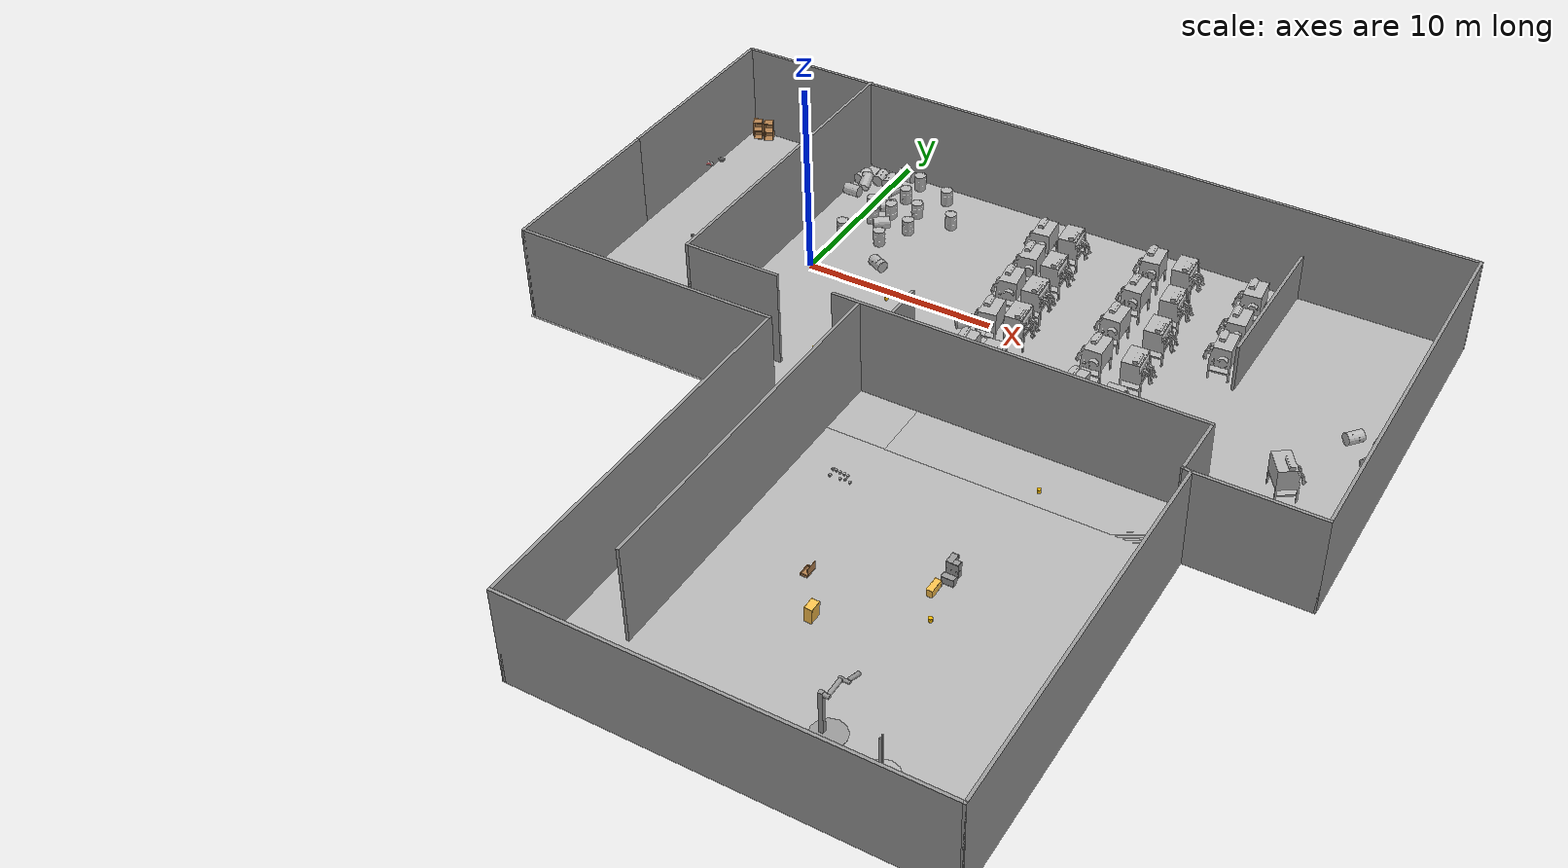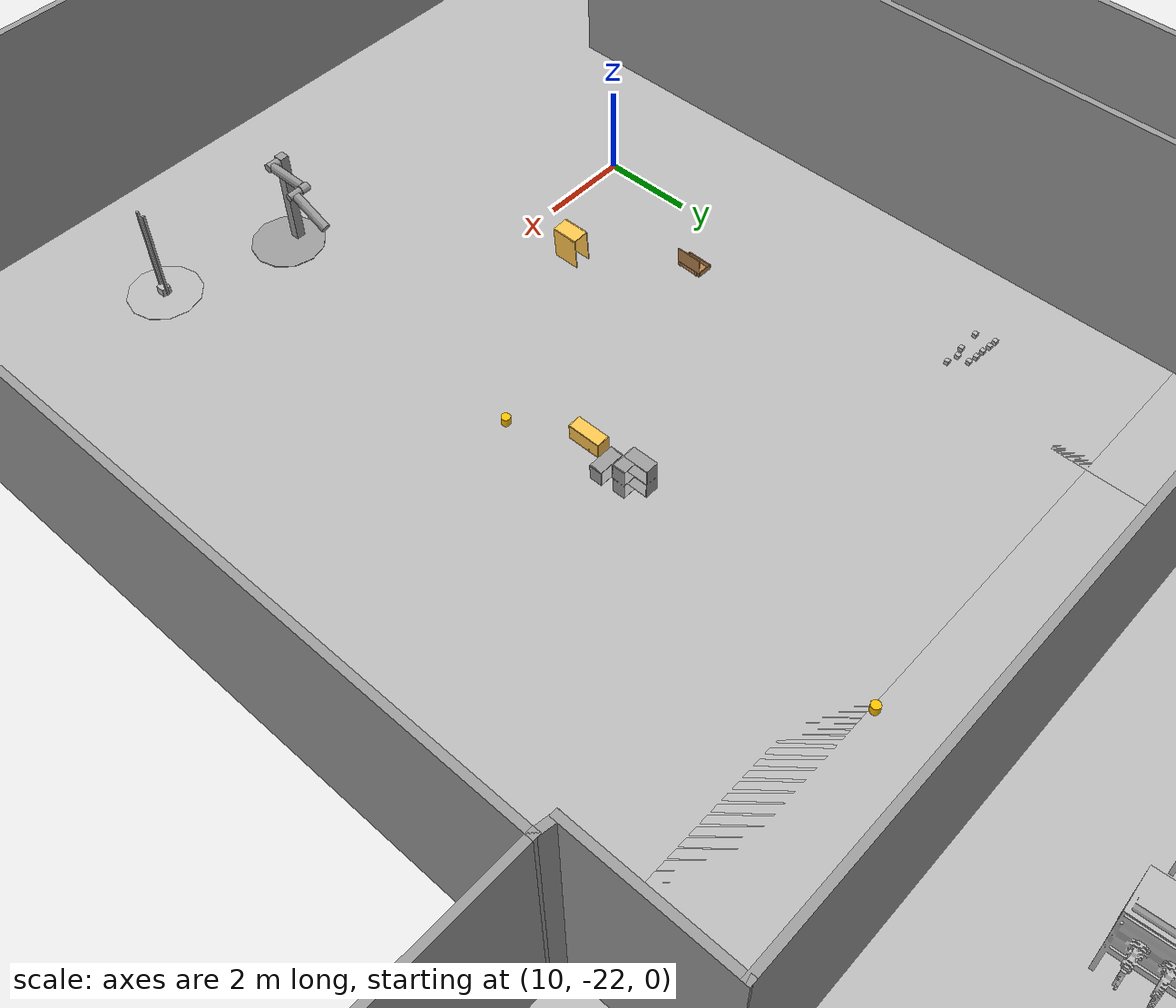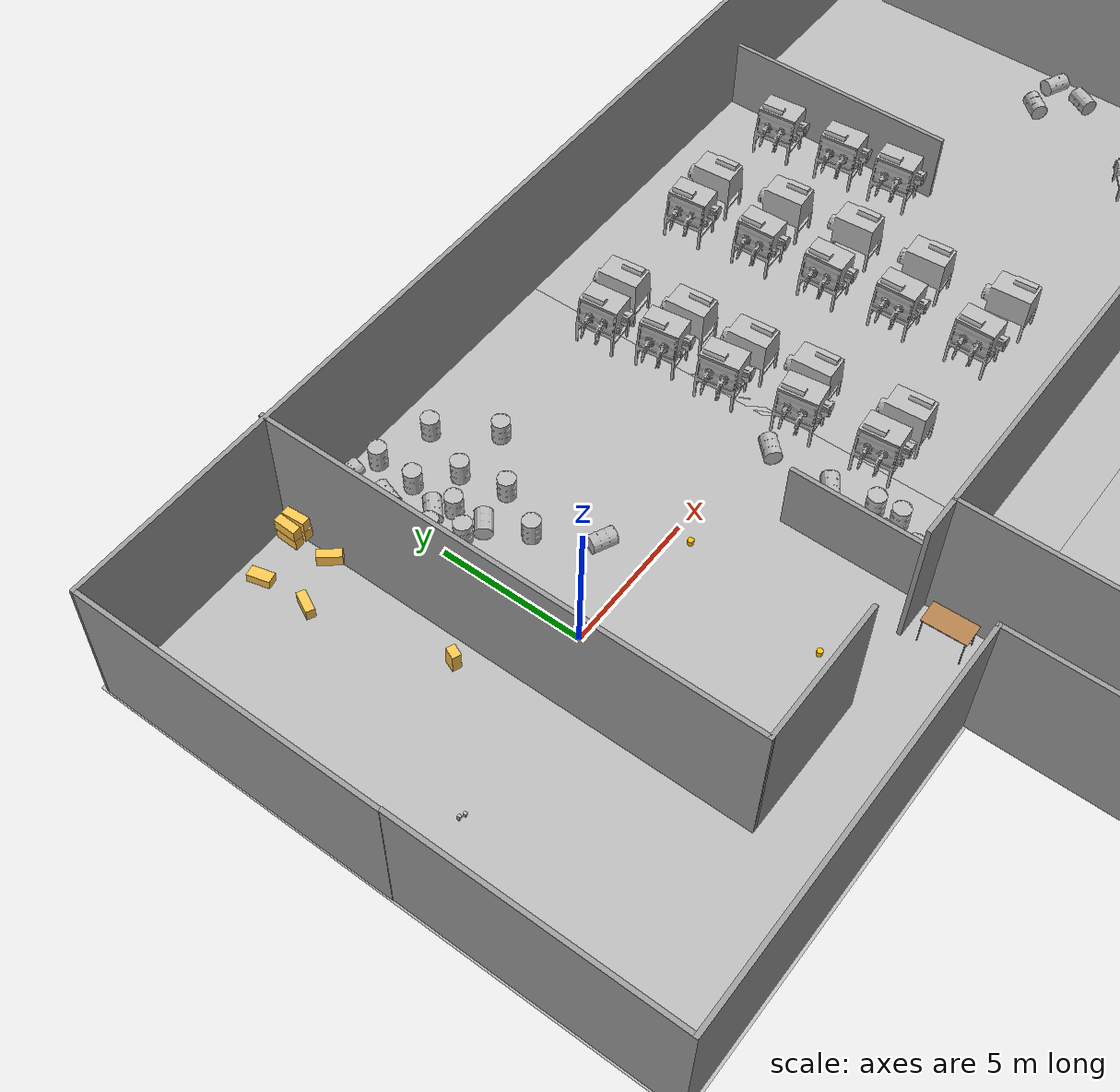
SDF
<sdf version="1.7">
 <world name="default">
  <light name="sun" type="directional">
   <pose>0 0 10 0 -0 0</pose>
   <diffuse>0.8 0.8 0.8 1</diffuse>
   <specular>0.2 0.2 0.2 1</specular>
   <attenuation>
    <range>1000</range>
    <constant>0.9</constant>
    <linear>0.01</linear>
    <quadratic>0.001</quadratic>
   </attenuation>
   <direction>-0.5 0.1 -0.9</direction>
   <spot><inner_angle>0</inner_angle><outer_angle>0</outer_angle><falloff>0</falloff></spot>
  </light>
  <model name="ground_plane">
   <static>1</static>
   <link name="link">
    <collision name="collision">
     <geometry><plane><normal>0 0 1</normal><size>100 100</size></plane></geometry>
     <surface><friction><ode><mu>100</mu><mu2>50</mu2></ode></friction></surface>
    </collision>
    <visual name="visual">
     <cast_shadows>0</cast_shadows>
     <geometry><plane><normal>0 0 1</normal><size>100 100</size></plane></geometry>
     <material>
      <script><uri>file://media/materials/scripts/gazebo.material</uri><name>Gazebo/Grey</name></script>
     </material>
    </visual>
   </link>
  </model>
  <gravity>0 0 -9.8</gravity>
  <magnetic_field>6e-06 2.3e-05 -4.2e-05</magnetic_field>
  <atmosphere type="adiabatic"/>
  <physics type="ode">
   <max_step_size>0.001</max_step_size>
   <real_time_factor>1</real_time_factor>
   <real_time_update_rate>1000</real_time_update_rate>
  </physics>
  <scene><ambient>0.4 0.4 0.4 1</ambient><background>0.7 0.7 0.7 1</background><shadows>1</shadows></scene>
  <audio><device>default</device></audio>
  <spherical_coordinates>
   <surface_model>EARTH_WGS84</surface_model>
   <latitude_deg>0</latitude_deg>
   <longitude_deg>0</longitude_deg>
   <elevation>0</elevation>
   <heading_deg>0</heading_deg>
  </spherical_coordinates>
  <model name="large_room_demo">
   <pose>10.4026 -9.94141 0 0 -0 0</pose>
   <link name="Wall_1">
    <collision name="Wall_1_Collision">
     <geometry><box><size>9.25 0.15 5</size></box></geometry>
     <pose>0 0 2.5 0 -0 0</pose>
    </collision>
    <visual name="Wall_1_Visual">
     <pose>0 0 2.5 0 -0 0</pose>
     <geometry><box><size>9.25 0.15 5</size></box></geometry>
     <material>
      <script><uri>file://media/materials/scripts/gazebo.material</uri><name>Gazebo/Grey</name></script>
      <ambient>1 1 1 1</ambient>
     </material>
     <meta><layer>0</layer></meta>
    </visual>
    <pose>-19.766 4.391 0 0 -0 -1.5708</pose>
   </link>
   <link name="Wall_11">
    <collision name="Wall_11_Collision">
     <geometry><box><size>17 0.15 5</size></box></geometry>
     <pose>0 0 2.5 0 -0 0</pose>
    </collision>
    <visual name="Wall_11_Visual">
     <pose>0 0 2.5 0 -0 0</pose>
     <geometry><box><size>17 0.15 5</size></box></geometry>
     <material>
      <script><uri>file://media/materials/scripts/gazebo.material</uri><name>Gazebo/Grey</name></script>
      <ambient>1 1 1 1</ambient>
     </material>
     <meta><layer>0</layer></meta>
    </visual>
    <pose>-12.466 11.084 0 0 -0 -1.5708</pose>
   </link>
   <link name="Wall_12">
    <collision name="Wall_12_Collision">
     <geometry><box><size>5 0.15 5</size></box></geometry>
     <pose>0 0 2.5 0 -0 0</pose>
    </collision>
    <visual name="Wall_12_Visual">
     <pose>0 0 2.5 0 -0 0</pose>
     <geometry><box><size>5 0.15 5</size></box></geometry>
     <material>
      <script><uri>file://media/materials/scripts/gazebo.material</uri><name>Gazebo/Grey</name></script>
      <ambient>1 1 1 1</ambient>
     </material>
     <meta><layer>0</layer></meta>
    </visual>
    <pose>-10.041 2.659 0 0 -0 0</pose>
   </link>
   <link name="Wall_15">
    <collision name="Wall_15_Collision">
     <geometry><box><size>1.5 0.15 5</size></box></geometry>
     <pose>0 0 2.5 0 -0 0</pose>
    </collision>
    <visual name="Wall_15_Visual">
     <pose>0 0 2.5 0 -0 0</pose>
     <geometry><box><size>1.5 0.15 5</size></box></geometry>
     <material>
      <script><uri>file://media/materials/scripts/gazebo.material</uri><name>Gazebo/Grey</name></script>
      <ambient>1 1 1 1</ambient>
     </material>
     <meta><layer>0</layer></meta>
    </visual>
    <pose>-3.97 2.751 0 0 -0 0</pose>
   </link>
   <link name="Wall_16">
    <collision name="Wall_16_Collision">
     <geometry><box><size>18.2497 0.15 5</size></box></geometry>
     <pose>0 0 2.5 0 -0 0</pose>
    </collision>
    <visual name="Wall_16_Visual">
     <pose>0 0 2.5 0 -0 0</pose>
     <geometry><box><size>18.2497 0.15 5</size></box></geometry>
     <material>
      <script><uri>file://media/materials/scripts/gazebo.material</uri><name>Gazebo/Grey</name></script>
      <ambient>1 1 1 1</ambient>
     </material>
     <meta><layer>0</layer></meta>
    </visual>
    <pose>-3.295 -6.299 0 0 -0 -1.5708</pose>
   </link>
   <link name="Wall_18">
    <collision name="Wall_18_Collision">
     <geometry><box><size>17 0.15 5</size></box></geometry>
     <pose>0 0 2.5 0 -0 0</pose>
    </collision>
    <visual name="Wall_18_Visual">
     <pose>0 0 2.5 0 -0 0</pose>
     <geometry><box><size>17 0.15 5</size></box></geometry>
     <material>
      <script><uri>file://media/materials/scripts/gazebo.material</uri><name>Gazebo/Grey</name></script>
      <ambient>1 1 1 1</ambient>
     </material>
     <meta><layer>0</layer></meta>
    </visual>
    <pose>5.13 2.751 0 0 -0 0</pose>
   </link>
   <link name="Wall_19">
    <collision name="Wall_19_Collision">
     <geometry><box><size>3.25 0.15 5</size></box></geometry>
     <pose>0 0 2.5 0 -0 0</pose>
    </collision>
    <visual name="Wall_19_Visual">
     <pose>0 0 2.5 0 -0 0</pose>
     <geometry><box><size>3.25 0.15 5</size></box></geometry>
     <material>
      <script><uri>file://media/materials/scripts/gazebo.material</uri><name>Gazebo/Grey</name></script>
      <ambient>1 1 1 1</ambient>
     </material>
     <meta><layer>0</layer></meta>
    </visual>
    <pose>13.555 1.201 0 0 -0 -1.5708</pose>
   </link>
   <link name="Wall_2">
    <collision name="Wall_2_Collision">
     <geometry><box><size>13.75 0.15 5</size></box></geometry>
     <pose>0 0 2.5 0 -0 0</pose>
    </collision>
    <visual name="Wall_2_Visual">
     <pose>0 0 2.5 0 -0 0</pose>
     <geometry><box><size>13.75 0.15 5</size></box></geometry>
     <material>
      <script><uri>file://media/materials/scripts/gazebo.material</uri><name>Gazebo/Grey</name></script>
      <ambient>1 1 1 1</ambient>
     </material>
     <meta><layer>0</layer></meta>
    </visual>
    <pose>-12.966 -0.159 0 0 -0 0</pose>
   </link>
   <link name="Wall_20">
    <collision name="Wall_20_Collision">
     <geometry><box><size>0.533873 0.15 5</size></box></geometry>
     <pose>0 0 2.5 0 -0 0</pose>
    </collision>
    <visual name="Wall_20_Visual">
     <pose>0 0 2.5 0 -0 0</pose>
     <geometry><box><size>0.533873 0.15 5</size></box></geometry>
     <material>
      <script><uri>file://media/materials/scripts/gazebo.material</uri><name>Gazebo/Grey</name></script>
      <ambient>1 1 1 1</ambient>
     </material>
     <meta><layer>0</layer></meta>
    </visual>
    <pose>13.7445 -0.379 0 0 -0 -0.157008</pose>
   </link>
   <link name="Wall_22">
    <collision name="Wall_22_Collision">
     <geometry><box><size>8.25 0.15 2.5</size></box></geometry>
     <pose>0 0 1.25 0 -0 0</pose>
    </collision>
    <visual name="Wall_22_Visual">
     <pose>0 0 1.25 0 -0 0</pose>
     <geometry><box><size>8.25 0.15 2.5</size></box></geometry>
     <material>
      <script><uri>file://media/materials/scripts/gazebo.material</uri><name>Gazebo/Grey</name></script>
      <ambient>1 1 1 1</ambient>
     </material>
     <meta><layer>0</layer></meta>
    </visual>
    <pose>11.5445 15.3019 0 0 -0 -1.5708</pose>
   </link>
   <link name="Wall_24">
    <collision name="Wall_24_Collision">
     <geometry><box><size>5 0.15 2.5</size></box></geometry>
     <pose>0 0 1.25 0 -0 0</pose>
    </collision>
    <visual name="Wall_24_Visual">
     <pose>0 0 1.25 0 -0 0</pose>
     <geometry><box><size>5 0.15 2.5</size></box></geometry>
     <material>
      <script><uri>file://media/materials/scripts/gazebo.material</uri><name>Gazebo/Grey</name></script>
      <ambient>1 1 1 1</ambient>
     </material>
     <meta><layer>0</layer></meta>
    </visual>
    <pose>-3.295 5.176 0 0 -0 1.5708</pose>
   </link>
   <link name="Wall_3">
    <collision name="Wall_3_Collision">
     <geometry><box><size>19.5 0.15 5</size></box></geometry>
     <pose>0 0 2.5 0 -0 0</pose>
    </collision>
    <visual name="Wall_3_Visual">
     <pose>0 0 2.5 0 -0 0</pose>
     <geometry><box><size>19.5 0.15 5</size></box></geometry>
     <material>
      <script><uri>file://media/materials/scripts/gazebo.material</uri><name>Gazebo/Grey</name></script>
      <ambient>1 1 1 1</ambient>
     </material>
     <meta><layer>0</layer></meta>
    </visual>
    <pose>-6.166 -9.834 0 0 -0 -1.5708</pose>
   </link>
   <link name="Wall_4">
    <collision name="Wall_4_Collision">
     <geometry><box><size>20.25 0.15 5</size></box></geometry>
     <pose>0 0 2.5 0 -0 0</pose>
    </collision>
    <visual name="Wall_4_Visual">
     <pose>0 0 2.5 0 -0 0</pose>
     <geometry><box><size>20.25 0.15 5</size></box></geometry>
     <material>
      <script><uri>file://media/materials/scripts/gazebo.material</uri><name>Gazebo/Grey</name></script>
      <ambient>1 1 1 1</ambient>
     </material>
     <meta><layer>0</layer></meta>
    </visual>
    <pose>3.884 -19.509 0 0 -0 0</pose>
   </link>
   <link name="Wall_5">
    <collision name="Wall_5_Collision">
     <geometry><box><size>19.25 0.15 5</size></box></geometry>
     <pose>0 0 2.5 0 -0 0</pose>
    </collision>
    <visual name="Wall_5_Visual">
     <pose>0 0 2.5 0 -0 0</pose>
     <geometry><box><size>19.25 0.15 5</size></box></geometry>
     <material>
      <script><uri>file://media/materials/scripts/gazebo.material</uri><name>Gazebo/Grey</name></script>
      <ambient>1 1 1 1</ambient>
     </material>
     <meta><layer>0</layer></meta>
    </visual>
    <pose>13.934 -9.959 0 0 -0 1.5708</pose>
   </link>
   <link name="Wall_6">
    <collision name="Wall_6_Collision">
     <geometry><box><size>6 0.15 5</size></box></geometry>
     <pose>0 0 2.5 0 -0 0</pose>
    </collision>
    <visual name="Wall_6_Visual">
     <pose>0 0 2.5 0 -0 0</pose>
     <geometry><box><size>6 0.15 5</size></box></geometry>
     <material>
      <script><uri>file://media/materials/scripts/gazebo.material</uri><name>Gazebo/Grey</name></script>
      <ambient>1 1 1 1</ambient>
     </material>
     <meta><layer>0</layer></meta>
    </visual>
    <pose>16.859 -0.409 0 0 -0 0</pose>
   </link>
   <link name="Wall_7">
    <collision name="Wall_7_Collision">
     <geometry><box><size>20 0.15 5</size></box></geometry>
     <pose>0 0 2.5 0 -0 0</pose>
    </collision>
    <visual name="Wall_7_Visual">
     <pose>0 0 2.5 0 -0 0</pose>
     <geometry><box><size>20 0.15 5</size></box></geometry>
     <material>
      <script><uri>file://media/materials/scripts/gazebo.material</uri><name>Gazebo/Grey</name></script>
      <ambient>1 1 1 1</ambient>
     </material>
     <meta><layer>0</layer></meta>
    </visual>
    <pose>19.784 9.516 0 0 -0 1.5708</pose>
   </link>
   <link name="Wall_8">
    <collision name="Wall_8_Collision">
     <geometry><box><size>39.718 0.15 5</size></box></geometry>
     <pose>0 0 2.5 0 -0 0</pose>
    </collision>
    <visual name="Wall_8_Visual">
     <pose>0 0 2.5 0 -0 0</pose>
     <geometry><box><size>39.718 0.15 5</size></box></geometry>
     <material>
      <script><uri>file://media/materials/scripts/gazebo.material</uri><name>Gazebo/Grey</name></script>
      <ambient>1 1 1 1</ambient>
     </material>
     <meta><layer>0</layer></meta>
    </visual>
    <pose>0 19.4235 0 0 -0 -3.14071</pose>
   </link>
   <link name="Wall_9">
    <collision name="Wall_9_Collision">
     <geometry><box><size>10.5 0.15 5</size></box></geometry>
     <pose>0 0 2.5 0 -0 0</pose>
    </collision>
    <visual name="Wall_9_Visual">
     <pose>0 0 2.5 0 -0 0</pose>
     <geometry><box><size>10.5 0.15 5</size></box></geometry>
     <material>
      <script><uri>file://media/materials/scripts/gazebo.material</uri><name>Gazebo/Grey</name></script>
      <ambient>1 1 1 1</ambient>
     </material>
     <meta><layer>0</layer></meta>
    </visual>
    <pose>-19.784 14.231 0 0 -0 -1.5708</pose>
   </link>
   <static>1</static>
  </model>
  <model name="Box_15x30">
   <link name="Wall">
    <pose>0 0 0.1985 0 -0 0</pose>
    <inertial>
     <mass>5</mass>
     <inertia><ixx>0.3089</ixx><iyy>0.1022</iyy><izz>0.2797</izz><ixy>0</ixy><ixz>0</ixz><iyz>0</iyz></inertia>
    </inertial>
    <collision name="Wall_Collision"><geometry><box><size>0.296 0.764 0.397</size></box></geometry></collision>
    <visual name="Wall_Visual">
     <geometry><box><size>0.296 0.764 0.397</size></box></geometry>
     <material>
      <script><uri>file://media/materials/scripts/gazebo.material</uri><name>Gazebo/Grey</name></script>
      <ambient>1 0.764706 0.305882 1</ambient>
     </material>
    </visual>
   </link>
   <static>1</static>
   <pose>-3.02054 6.65631 1.55151 0 -0 0.691063</pose>
  </model>
  <model name="cabinet">
   <static>1</static>
   <link name="cabinet_bottom_plate">
    <inertial>
     <pose>0 0 -1 0 -0 0</pose>
     <inertia><ixx>2.05</ixx><ixy>0</ixy><ixz>0</ixz><iyy>2.05</iyy><iyz>0</iyz><izz>2.05</izz></inertia>
     <mass>25</mass>
    </inertial>
    <collision name="cabinet_bottom_plate_geom">
     <pose>0 0 0.01 0 -0 0</pose>
     <geometry><box><size>0.45 0.45 0.02</size></box></geometry>
    </collision>
    <visual name="cabinet_bottom_plate_geom_visual">
     <pose>0 0 0.01 0 -0 0</pose>
     <geometry><box><size>0.45 0.45 0.02</size></box></geometry>
     <material>
      <script><uri>file://media/materials/scripts/gazebo.material</uri><name>Gazebo/Wood</name></script>
     </material>
    </visual>
    <collision name="cabinet_bottom_plate_geom_cabinet_back_plate">
     <pose>0.235 0 0.51 0 -0 0</pose>
     <geometry><box><size>0.02 0.45 1.02</size></box></geometry>
    </collision>
    <visual name="cabinet_bottom_plate_geom_cabinet_back_plate_visual">
     <pose>0.235 0 0.51 0 -0 0</pose>
     <geometry><box><size>0.02 0.45 1.02</size></box></geometry>
     <material>
      <script><uri>file://media/materials/scripts/gazebo.material</uri><name>Gazebo/Wood</name></script>
     </material>
    </visual>
    <collision name="cabinet_bottom_plate_geom_cabinet_left_plate">
     <pose>0 0.235 0.51 0 -0 0</pose>
     <geometry><box><size>0.45 0.02 1.02</size></box></geometry>
    </collision>
    <visual name="cabinet_bottom_plate_geom_cabinet_left_plate_visual">
     <pose>0 0.235 0.51 0 -0 0</pose>
     <geometry><box><size>0.45 0.02 1.02</size></box></geometry>
     <material>
      <script><uri>file://media/materials/scripts/gazebo.material</uri><name>Gazebo/Wood</name></script>
     </material>
    </visual>
    <collision name="cabinet_bottom_plate_geom_cabinet_middle_plate">
     <pose>0 0 0.51 0 -0 0</pose>
     <geometry><box><size>0.45 0.45 0.02</size></box></geometry>
    </collision>
    <visual name="cabinet_bottom_plate_geom_cabinet_middle_plate_visual">
     <pose>0 0 0.51 0 -0 0</pose>
     <geometry><box><size>0.45 0.45 0.02</size></box></geometry>
     <material>
      <script><uri>file://media/materials/scripts/gazebo.material</uri><name>Gazebo/Wood</name></script>
     </material>
    </visual>
    <collision name="cabinet_bottom_plate_geom_cabinet_right_plate">
     <pose>0 -0.235 0.51 0 -0 0</pose>
     <geometry><box><size>0.45 0.02 1.02</size></box></geometry>
    </collision>
    <visual name="cabinet_bottom_plate_geom_cabinet_right_plate_visual">
     <pose>0 -0.235 0.51 0 -0 0</pose>
     <geometry><box><size>0.45 0.02 1.02</size></box></geometry>
     <material>
      <script><uri>file://media/materials/scripts/gazebo.material</uri><name>Gazebo/Wood</name></script>
     </material>
    </visual>
    <collision name="cabinet_bottom_plate_geom_cabinet_top_plate">
     <pose>0 0 1.01 0 -0 0</pose>
     <geometry><box><size>0.45 0.45 0.02</size></box></geometry>
    </collision>
    <visual name="cabinet_bottom_plate_geom_cabinet_top_plate_visual">
     <pose>0 0 1.01 0 -0 0</pose>
     <geometry><box><size>0.45 0.45 0.02</size></box></geometry>
     <material>
      <script><uri>file://media/materials/scripts/gazebo.material</uri><name>Gazebo/Wood</name></script>
     </material>
    </visual>
   </link>
   <pose>-8.77211 8.83368 0 0 -0 2</pose>
  </model>
  <model name="cabinet_clone">
   <static>1</static>
   <link name="cabinet_bottom_plate">
    <inertial>
     <pose>0 0 -1 0 -0 0</pose>
     <inertia><ixx>2.05</ixx><ixy>0</ixy><ixz>0</ixz><iyy>2.05</iyy><iyz>0</iyz><izz>2.05</izz></inertia>
     <mass>25</mass>
    </inertial>
    <collision name="cabinet_bottom_plate_geom">
     <pose>0 0 0.01 0 -0 0</pose>
     <geometry><box><size>0.45 0.45 0.02</size></box></geometry>
    </collision>
    <visual name="cabinet_bottom_plate_geom_visual">
     <pose>0 0 0.01 0 -0 0</pose>
     <geometry><box><size>0.45 0.45 0.02</size></box></geometry>
     <material>
      <script><uri>file://media/materials/scripts/gazebo.material</uri><name>Gazebo/Wood</name></script>
     </material>
    </visual>
    <collision name="cabinet_bottom_plate_geom_cabinet_back_plate">
     <pose>0.235 0 0.51 0 -0 0</pose>
     <geometry><box><size>0.02 0.45 1.02</size></box></geometry>
    </collision>
    <visual name="cabinet_bottom_plate_geom_cabinet_back_plate_visual">
     <pose>0.235 0 0.51 0 -0 0</pose>
     <geometry><box><size>0.02 0.45 1.02</size></box></geometry>
     <material>
      <script><uri>file://media/materials/scripts/gazebo.material</uri><name>Gazebo/Wood</name></script>
     </material>
    </visual>
    <collision name="cabinet_bottom_plate_geom_cabinet_left_plate">
     <pose>0 0.235 0.51 0 -0 0</pose>
     <geometry><box><size>0.45 0.02 1.02</size></box></geometry>
    </collision>
    <visual name="cabinet_bottom_plate_geom_cabinet_left_plate_visual">
     <pose>0 0.235 0.51 0 -0 0</pose>
     <geometry><box><size>0.45 0.02 1.02</size></box></geometry>
     <material>
      <script><uri>file://media/materials/scripts/gazebo.material</uri><name>Gazebo/Wood</name></script>
     </material>
    </visual>
    <collision name="cabinet_bottom_plate_geom_cabinet_middle_plate">
     <pose>0 0 0.51 0 -0 0</pose>
     <geometry><box><size>0.45 0.45 0.02</size></box></geometry>
    </collision>
    <visual name="cabinet_bottom_plate_geom_cabinet_middle_plate_visual">
     <pose>0 0 0.51 0 -0 0</pose>
     <geometry><box><size>0.45 0.45 0.02</size></box></geometry>
     <material>
      <script><uri>file://media/materials/scripts/gazebo.material</uri><name>Gazebo/Wood</name></script>
     </material>
    </visual>
    <collision name="cabinet_bottom_plate_geom_cabinet_right_plate">
     <pose>0 -0.235 0.51 0 -0 0</pose>
     <geometry><box><size>0.45 0.02 1.02</size></box></geometry>
    </collision>
    <visual name="cabinet_bottom_plate_geom_cabinet_right_plate_visual">
     <pose>0 -0.235 0.51 0 -0 0</pose>
     <geometry><box><size>0.45 0.02 1.02</size></box></geometry>
     <material>
      <script><uri>file://media/materials/scripts/gazebo.material</uri><name>Gazebo/Wood</name></script>
     </material>
    </visual>
    <collision name="cabinet_bottom_plate_geom_cabinet_top_plate">
     <pose>0 0 1.01 0 -0 0</pose>
     <geometry><box><size>0.45 0.45 0.02</size></box></geometry>
    </collision>
    <visual name="cabinet_bottom_plate_geom_cabinet_top_plate_visual">
     <pose>0 0 1.01 0 -0 0</pose>
     <geometry><box><size>0.45 0.45 0.02</size></box></geometry>
     <material>
      <script><uri>file://media/materials/scripts/gazebo.material</uri><name>Gazebo/Wood</name></script>
     </material>
    </visual>
   </link>
   <pose>-8.20771 9.0077 0 0 -0 2</pose>
  </model>
  <model name="coffee_box">
   <link name="link_0">
    <visual name="visual">
     <pose>0 0 0.06 0 -0 0</pose>
     <geometry><cylinder><radius>0.04</radius><length>0.12</length></cylinder></geometry>
     <material>
      <script>
       <uri>model://coffee_box/materials/scripts</uri>
       <uri>model://coffee_box/materials/textures</uri>
       <name>coffee_pat</name>
      </script>
     </material>
    </visual>
    <collision name="collision">
     <geometry><cylinder><radius>0.04</radius><length>0.12</length></cylinder></geometry>
    </collision>
   </link>
   <static>1</static>
   <pose>-8.39102 4.9248 0.776361 0 -0 0</pose>
  </model>
  <model name="coffee_box_clone">
   <link name="link_0">
    <visual name="visual">
     <pose>0 0 0.06 0 -0 0</pose>
     <geometry><cylinder><radius>0.04</radius><length>0.12</length></cylinder></geometry>
     <material>
      <script>
       <uri>model://coffee_box/materials/scripts</uri>
       <uri>model://coffee_box/materials/textures</uri>
       <name>coffee_pat</name>
      </script>
     </material>
    </visual>
    <collision name="collision">
     <geometry><cylinder><radius>0.04</radius><length>0.12</length></cylinder></geometry>
    </collision>
   </link>
   <static>1</static>
   <pose>-8.4911 4.86199 0.776361 0 -0 0</pose>
  </model>
  <model name="coffee_box_clone_0">
   <link name="link_0">
    <visual name="visual">
     <pose>0 0 0.06 0 -0 0</pose>
     <geometry><cylinder><radius>0.04</radius><length>0.12</length></cylinder></geometry>
     <material>
      <script>
       <uri>model://coffee_box/materials/scripts</uri>
       <uri>model://coffee_box/materials/textures</uri>
       <name>coffee_pat</name>
      </script>
     </material>
    </visual>
    <collision name="collision">
     <geometry><cylinder><radius>0.04</radius><length>0.12</length></cylinder></geometry>
    </collision>
   </link>
   <static>1</static>
   <pose>-8.40065 4.83683 0.776361 0 -0 0</pose>
  </model>
  <model name="coffee_box_clone_1">
   <link name="link_0">
    <visual name="visual">
     <pose>0 0 0.06 0 -0 0</pose>
     <geometry><cylinder><radius>0.04</radius><length>0.12</length></cylinder></geometry>
     <material>
      <script>
       <uri>model://coffee_box/materials/scripts</uri>
       <uri>model://coffee_box/materials/textures</uri>
       <name>coffee_pat</name>
      </script>
     </material>
    </visual>
    <collision name="collision">
     <geometry><cylinder><radius>0.04</radius><length>0.12</length></cylinder></geometry>
    </collision>
   </link>
   <static>1</static>
   <pose>-8.48638 4.76785 0.776361 0 -0 0</pose>
  </model>
  <model name="coffee_box_clone_2">
   <link name="link_0">
    <visual name="visual">
     <pose>0 0 0.06 0 -0 0</pose>
     <geometry><cylinder><radius>0.04</radius><length>0.12</length></cylinder></geometry>
     <material>
      <script>
       <uri>model://coffee_box/materials/scripts</uri>
       <uri>model://coffee_box/materials/textures</uri>
       <name>coffee_pat</name>
      </script>
     </material>
    </visual>
    <collision name="collision">
     <geometry><cylinder><radius>0.04</radius><length>0.12</length></cylinder></geometry>
    </collision>
   </link>
   <static>1</static>
   <pose>-8.63013 4.82993 0.776361 0 -0 0</pose>
  </model>
  <model name="coffee_box_clone_3">
   <link name="link_0">
    <visual name="visual">
     <pose>0 0 0.06 0 -0 0</pose>
     <geometry><cylinder><radius>0.04</radius><length>0.12</length></cylinder></geometry>
     <material>
      <script>
       <uri>model://coffee_box/materials/scripts</uri>
       <uri>model://coffee_box/materials/textures</uri>
       <name>coffee_pat</name>
      </script>
     </material>
    </visual>
    <collision name="collision">
     <geometry><cylinder><radius>0.04</radius><length>0.12</length></cylinder></geometry>
    </collision>
   </link>
   <static>1</static>
   <pose>-8.66125 4.92731 0.776361 0 -0 0</pose>
  </model>
  <model name="biscuit_box">
   <link name="link">
    <pose>0 0 0.025 0 -0 0</pose>
    <visual name="visual">
     <geometry><box><size>0.2 0.15 0.05</size></box></geometry>
     <material>
      <ambient>0.423 0.019 0.035 1</ambient>
      <diffuse>0.423 0.019 0.035 1</diffuse>
      <specular>0.01 0.01 0.01 1</specular>
      <emissive>0 0 0 1</emissive>
     </material>
    </visual>
    <collision name="collision"><geometry><box><size>0.1 0.1 0.15</size></box></geometry></collision>
   </link>
   <link name="link_1">
    <pose>0 0 0.05 0 -0 0</pose>
    <visual name="visual">
     <geometry><box><size>0.2 0.15 0.001</size></box></geometry>
     <material>
      <script>
       <uri>model://biscuit_box/materials/scripts</uri>
       <uri>model://biscuit_box/materials/textures</uri>
       <name>biscuit_pat</name>
      </script>
     </material>
    </visual>
    <collision name="collision"><geometry><box><size>0.1 0.1 0.15</size></box></geometry></collision>
   </link>
   <static>1</static>
   <pose>-8.88673 4.23471 0.838766 0 0 -0.080076</pose>
  </model>
  <model name="biscuit_box_clone_0">
   <link name="link">
    <pose>0 0 0.025 0 -0 0</pose>
    <visual name="visual">
     <geometry><box><size>0.2 0.15 0.05</size></box></geometry>
     <material>
      <ambient>0.423 0.019 0.035 1</ambient>
      <diffuse>0.423 0.019 0.035 1</diffuse>
      <specular>0.01 0.01 0.01 1</specular>
      <emissive>0 0 0 1</emissive>
     </material>
    </visual>
    <collision name="collision"><geometry><box><size>0.1 0.1 0.15</size></box></geometry></collision>
   </link>
   <link name="link_1">
    <pose>0 0 0.05 0 -0 0</pose>
    <visual name="visual">
     <geometry><box><size>0.2 0.15 0.001</size></box></geometry>
     <material>
      <script>
       <uri>model://biscuit_box/materials/scripts</uri>
       <uri>model://biscuit_box/materials/textures</uri>
       <name>biscuit_pat</name>
      </script>
     </material>
    </visual>
    <collision name="collision"><geometry><box><size>0.1 0.1 0.15</size></box></geometry></collision>
   </link>
   <static>1</static>
   <pose>-8.89674 4.23031 0.776684 0 -0 0</pose>
  </model>
  <model name="biscuit_box_clone_2">
   <link name="link">
    <pose>0 0 0.025 0 -0 0</pose>
    <visual name="visual">
     <geometry><box><size>0.2 0.15 0.05</size></box></geometry>
     <material>
      <ambient>0.423 0.019 0.035 1</ambient>
      <diffuse>0.423 0.019 0.035 1</diffuse>
      <specular>0.01 0.01 0.01 1</specular>
      <emissive>0 0 0 1</emissive>
     </material>
    </visual>
    <collision name="collision"><geometry><box><size>0.1 0.1 0.15</size></box></geometry></collision>
   </link>
   <link name="link_1">
    <pose>0 0 0.05 0 -0 0</pose>
    <visual name="visual">
     <geometry><box><size>0.2 0.15 0.001</size></box></geometry>
     <material>
      <script>
       <uri>model://biscuit_box/materials/scripts</uri>
       <uri>model://biscuit_box/materials/textures</uri>
       <name>biscuit_pat</name>
      </script>
     </material>
    </visual>
    <collision name="collision"><geometry><box><size>0.1 0.1 0.15</size></box></geometry></collision>
   </link>
   <static>1</static>
   <pose>-8.74577 4.22735 0.838766 0 0.906388 -0.080076</pose>
  </model>
  <model name="Box_15x30_clone">
   <link name="Wall">
    <pose>0 0 0.1985 0 -0 0</pose>
    <inertial>
     <mass>5</mass>
     <inertia><ixx>0.3089</ixx><iyy>0.1022</iyy><izz>0.2797</izz><ixy>0</ixy><ixz>0</ixz><iyz>0</iyz></inertia>
    </inertial>
    <collision name="Wall_Collision"><geometry><box><size>0.296 0.764 0.397</size></box></geometry></collision>
    <visual name="Wall_Visual">
     <geometry><box><size>0.296 0.764 0.397</size></box></geometry>
     <material>
      <script><uri>file://media/materials/scripts/gazebo.material</uri><name>Gazebo/Grey</name></script>
      <ambient>1 0.764706 0.305882 1</ambient>
     </material>
    </visual>
   </link>
   <static>1</static>
   <pose>-2.78141 8.03759 1.5515 0 0 -0.031938</pose>
  </model>
  <model name="Box_15x30_clone_clone">
   <link name="Wall">
    <pose>0 0 0.1985 0 -0 0</pose>
    <inertial>
     <mass>5</mass>
     <inertia><ixx>0.3089</ixx><iyy>0.1022</iyy><izz>0.2797</izz><ixy>0</ixy><ixz>0</ixz><iyz>0</iyz></inertia>
    </inertial>
    <collision name="Wall_Collision"><geometry><box><size>0.296 0.764 0.397</size></box></geometry></collision>
    <visual name="Wall_Visual">
     <geometry><box><size>0.296 0.764 0.397</size></box></geometry>
     <material>
      <script><uri>file://media/materials/scripts/gazebo.material</uri><name>Gazebo/Grey</name></script>
      <ambient>1 0.764706 0.305882 1</ambient>
     </material>
    </visual>
   </link>
   <static>1</static>
   <pose>-3.1629 8.04866 1.5515 0 0 -0.031938</pose>
  </model>
  <model name="Box_15x30_clone_clone_0">
   <link name="Wall">
    <pose>0 0 0.1985 0 -0 0</pose>
    <inertial>
     <mass>5</mass>
     <inertia><ixx>0.3089</ixx><iyy>0.1022</iyy><izz>0.2797</izz><ixy>0</ixy><ixz>0</ixz><iyz>0</iyz></inertia>
    </inertial>
    <collision name="Wall_Collision"><geometry><box><size>0.296 0.764 0.397</size></box></geometry></collision>
    <visual name="Wall_Visual">
     <geometry><box><size>0.296 0.764 0.397</size></box></geometry>
     <material>
      <script><uri>file://media/materials/scripts/gazebo.material</uri><name>Gazebo/Grey</name></script>
      <ambient>1 0.764706 0.305882 1</ambient>
     </material>
    </visual>
   </link>
   <static>1</static>
   <pose>-2.8223 8.04967 1.99212 0 -0 0.070577</pose>
  </model>
  <model name="Box_15x30_clone_clone_0_clone">
   <link name="Wall">
    <pose>0 0 0.1985 0 -0 0</pose>
    <inertial>
     <mass>5</mass>
     <inertia><ixx>0.3089</ixx><iyy>0.1022</iyy><izz>0.2797</izz><ixy>0</ixy><ixz>0</ixz><iyz>0</iyz></inertia>
    </inertial>
    <collision name="Wall_Collision"><geometry><box><size>0.296 0.764 0.397</size></box></geometry></collision>
    <visual name="Wall_Visual">
     <geometry><box><size>0.296 0.764 0.397</size></box></geometry>
     <material>
      <script><uri>file://media/materials/scripts/gazebo.material</uri><name>Gazebo/Grey</name></script>
      <ambient>1 0.764706 0.305882 1</ambient>
     </material>
    </visual>
   </link>
   <static>1</static>
   <pose>-3.18877 8.03993 1.99212 0 0 -0.031938</pose>
  </model>
  <model name="Box_15x30_clone_clone_clone">
   <link name="Wall">
    <pose>0 0 0.1985 0 -0 0</pose>
    <inertial>
     <mass>5</mass>
     <inertia><ixx>0.3089</ixx><iyy>0.1022</iyy><izz>0.2797</izz><ixy>0</ixy><ixz>0</ixz><iyz>0</iyz></inertia>
    </inertial>
    <collision name="Wall_Collision"><geometry><box><size>0.296 0.764 0.397</size></box></geometry></collision>
    <visual name="Wall_Visual">
     <geometry><box><size>0.296 0.764 0.397</size></box></geometry>
     <material>
      <script><uri>file://media/materials/scripts/gazebo.material</uri><name>Gazebo/Grey</name></script>
      <ambient>1 0.764706 0.305882 1</ambient>
     </material>
    </visual>
   </link>
   <static>1</static>
   <pose>-3.98125 6.92031 0.021086 0 0 -0.459084</pose>
  </model>
  <model name="Box_15x30_clone_clone_clone_clone">
   <link name="Wall">
    <pose>0 0 0.1985 0 -0 0</pose>
    <inertial>
     <mass>5</mass>
     <inertia><ixx>0.3089</ixx><iyy>0.1022</iyy><izz>0.2797</izz><ixy>0</ixy><ixz>0</ixz><iyz>0</iyz></inertia>
    </inertial>
    <collision name="Wall_Collision"><geometry><box><size>0.296 0.764 0.397</size></box></geometry></collision>
    <visual name="Wall_Visual">
     <geometry><box><size>0.296 0.764 0.397</size></box></geometry>
     <material>
      <script><uri>file://media/materials/scripts/gazebo.material</uri><name>Gazebo/Grey</name></script>
      <ambient>1 0.764706 0.305882 1</ambient>
     </material>
    </visual>
   </link>
   <static>1</static>
   <pose>-3.84843 8.68396 0.169655 0 -1.47913 0.262274</pose>
  </model>
  <model name="tea_box">
   <link name="link">
    <pose>0 0 0.075 0 -0 0</pose>
    <visual name="visual">
     <geometry><box><size>0.1 0.1 0.15</size></box></geometry>
     <material>
      <script>
       <uri>model://tea_box/materials/scripts</uri>
       <uri>model://tea_box/materials/textures</uri>
       <name>tea_pat</name>
      </script>
     </material>
    </visual>
    <collision name="collision"><geometry><box><size>0.1 0.1 0.15</size></box></geometry></collision>
   </link>
   <static>1</static>
   <pose>-6.38264 -0.920342 0 0 -0 0</pose>
  </model>
  <model name="tea_box_0">
   <link name="link">
    <pose>0 0 0.075 0 -0 0</pose>
    <visual name="visual">
     <geometry><box><size>0.1 0.1 0.15</size></box></geometry>
     <material>
      <script>
       <uri>model://tea_box/materials/scripts</uri>
       <uri>model://tea_box/materials/textures</uri>
       <name>tea_pat</name>
      </script>
     </material>
    </visual>
    <collision name="collision"><geometry><box><size>0.1 0.1 0.15</size></box></geometry></collision>
   </link>
   <static>1</static>
   <pose>-6.5734 -0.851757 0.00381 0 0.200112 0</pose>
  </model>
  <model name="table">
   <static>1</static>
   <link name="link">
    <collision name="surface">
     <pose>0 0 1 0 -0 0</pose>
     <geometry><box><size>1.5 0.8 0.03</size></box></geometry>
     <surface><friction><ode><mu>0.6</mu><mu2>0.6</mu2></ode></friction></surface>
    </collision>
    <visual name="visual1">
     <pose>0 0 1 0 -0 0</pose>
     <geometry><box><size>1.5 0.8 0.03</size></box></geometry>
     <material>
      <script><uri>file://media/materials/scripts/gazebo.material</uri><name>Gazebo/Wood</name></script>
     </material>
    </visual>
    <collision name="front_left_leg">
     <pose>0.68 0.38 0.5 0 -0 0</pose>
     <geometry><cylinder><radius>0.02</radius><length>1</length></cylinder></geometry>
    </collision>
    <visual name="front_left_leg">
     <pose>0.68 0.38 0.5 0 -0 0</pose>
     <geometry><cylinder><radius>0.02</radius><length>1</length></cylinder></geometry>
     <material>
      <script><uri>file://media/materials/scripts/gazebo.material</uri><name>Gazebo/Grey</name></script>
     </material>
    </visual>
    <collision name="front_right_leg">
     <pose>0.68 -0.38 0.5 0 -0 0</pose>
     <geometry><cylinder><radius>0.02</radius><length>1</length></cylinder></geometry>
    </collision>
    <visual name="front_right_leg">
     <pose>0.68 -0.38 0.5 0 -0 0</pose>
     <geometry><cylinder><radius>0.02</radius><length>1</length></cylinder></geometry>
     <material>
      <script><uri>file://media/materials/scripts/gazebo.material</uri><name>Gazebo/Grey</name></script>
     </material>
    </visual>
    <collision name="back_right_leg">
     <pose>-0.68 -0.38 0.5 0 -0 0</pose>
     <geometry><cylinder><radius>0.02</radius><length>1</length></cylinder></geometry>
    </collision>
    <visual name="back_right_leg">
     <pose>-0.68 -0.38 0.5 0 -0 0</pose>
     <geometry><cylinder><radius>0.02</radius><length>1</length></cylinder></geometry>
     <material>
      <script><uri>file://media/materials/scripts/gazebo.material</uri><name>Gazebo/Grey</name></script>
     </material>
    </visual>
    <collision name="back_left_leg">
     <pose>-0.68 0.38 0.5 0 -0 0</pose>
     <geometry><cylinder><radius>0.02</radius><length>1</length></cylinder></geometry>
    </collision>
    <visual name="back_left_leg">
     <pose>-0.68 0.38 0.5 0 -0 0</pose>
     <geometry><cylinder><radius>0.02</radius><length>1</length></cylinder></geometry>
     <material>
      <script><uri>file://media/materials/scripts/gazebo.material</uri><name>Gazebo/Grey</name></script>
     </material>
    </visual>
   </link>
   <pose>6.23222 -8.37348 0 0 -0 1.6</pose>
  </model>
  <model name="toxic_barrel">
   <static>0</static>
   <link name="link">
    <visual name="visual">
     <geometry><mesh><uri>model://toxic_barrel/meshes/barrel_red.obj</uri></mesh></geometry>
    </visual>
    <collision name="collision">
     <geometry><mesh><uri>model://toxic_barrel/meshes/barrel_red.obj</uri></mesh></geometry>
    </collision>
    <inertial>
     <inertia><ixx>1</ixx><ixy>0</ixy><ixz>0</ixz><iyy>1</iyy><iyz>0</iyz><izz>1</izz></inertia>
     <mass>1</mass>
    </inertial>
   </link>
   <pose>-1.62584 7.93495 0.306208 8e-06 -0.196378 -0.160984</pose>
  </model>
  <model name="toxic_barrel_clone">
   <static>0</static>
   <link name="link">
    <visual name="visual">
     <geometry><mesh><uri>model://toxic_barrel/meshes/barrel_red.obj</uri></mesh></geometry>
    </visual>
    <collision name="collision">
     <geometry><mesh><uri>model://toxic_barrel/meshes/barrel_red.obj</uri></mesh></geometry>
    </collision>
    <inertial>
     <inertia><ixx>1</ixx><ixy>0</ixy><ixz>0</ixz><iyy>1</iyy><iyz>0</iyz><izz>1</izz></inertia>
     <mass>1</mass>
    </inertial>
   </link>
   <pose>-0.152655 8.17784 0.306205 -1e-06 -0.589074 0.075545</pose>
  </model>
  <model name="toxic_barrel_clone_clone">
   <static>0</static>
   <link name="link">
    <visual name="visual">
     <geometry><mesh><uri>model://toxic_barrel/meshes/barrel_red.obj</uri></mesh></geometry>
    </visual>
    <collision name="collision">
     <geometry><mesh><uri>model://toxic_barrel/meshes/barrel_red.obj</uri></mesh></geometry>
    </collision>
    <inertial>
     <inertia><ixx>1</ixx><ixy>0</ixy><ixz>0</ixz><iyy>1</iyy><iyz>0</iyz><izz>1</izz></inertia>
     <mass>1</mass>
    </inertial>
   </link>
   <pose>0.356808 9.06526 0.306196 1e-06 -0.589078 1.4983</pose>
  </model>
  <model name="toxic_barrel_clone_clone_0">
   <static>0</static>
   <link name="link">
    <visual name="visual">
     <geometry><mesh><uri>model://toxic_barrel/meshes/barrel_red.obj</uri></mesh></geometry>
    </visual>
    <collision name="collision">
     <geometry><mesh><uri>model://toxic_barrel/meshes/barrel_red.obj</uri></mesh></geometry>
    </collision>
    <inertial>
     <inertia><ixx>1</ixx><ixy>0</ixy><ixz>0</ixz><iyy>1</iyy><iyz>0</iyz><izz>1</izz></inertia>
     <mass>1</mass>
    </inertial>
   </link>
   <pose>8.98441 -0.609743 0.306198 -3.14159 -0.981738 2.37214</pose>
  </model>
  <model name="toxic_barrel_clone_clone_1">
   <static>0</static>
   <link name="link">
    <visual name="visual">
     <geometry><mesh><uri>model://toxic_barrel/meshes/barrel_red.obj</uri></mesh></geometry>
    </visual>
    <collision name="collision">
     <geometry><mesh><uri>model://toxic_barrel/meshes/barrel_red.obj</uri></mesh></geometry>
    </collision>
    <inertial>
     <inertia><ixx>1</ixx><ixy>0</ixy><ixz>0</ixz><iyy>1</iyy><iyz>0</iyz><izz>1</izz></inertia>
     <mass>1</mass>
    </inertial>
   </link>
   <pose>-0.749007 8.25217 0.306198 4e-06 -0.589051 0.05948</pose>
  </model>
  <model name="toxic_barrel_clone_clone_2">
   <static>0</static>
   <link name="link">
    <visual name="visual">
     <geometry><mesh><uri>model://toxic_barrel/meshes/barrel_red.obj</uri></mesh></geometry>
    </visual>
    <collision name="collision">
     <geometry><mesh><uri>model://toxic_barrel/meshes/barrel_red.obj</uri></mesh></geometry>
    </collision>
    <inertial>
     <inertia><ixx>1</ixx><ixy>0</ixy><ixz>0</ixz><iyy>1</iyy><iyz>0</iyz><izz>1</izz></inertia>
     <mass>1</mass>
    </inertial>
   </link>
   <pose>0.416552 7.59535 0.306203 -5e-06 -0.589071 -0.305276</pose>
  </model>
  <model name="toxic_barrel_clone_clone_3">
   <static>0</static>
   <link name="link">
    <visual name="visual">
     <geometry><mesh><uri>model://toxic_barrel/meshes/barrel_red.obj</uri></mesh></geometry>
    </visual>
    <collision name="collision">
     <geometry><mesh><uri>model://toxic_barrel/meshes/barrel_red.obj</uri></mesh></geometry>
    </collision>
    <inertial>
     <inertia><ixx>1</ixx><ixy>0</ixy><ixz>0</ixz><iyy>1</iyy><iyz>0</iyz><izz>1</izz></inertia>
     <mass>1</mass>
    </inertial>
   </link>
   <pose>8.83956 -2.86271 0.306203 -8e-06 -0.981729 -0.994421</pose>
  </model>
  <model name="toxic_barrel_clone_clone_4">
   <static>0</static>
   <link name="link">
    <visual name="visual">
     <geometry><mesh><uri>model://toxic_barrel/meshes/barrel_red.obj</uri></mesh></geometry>
    </visual>
    <collision name="collision">
     <geometry><mesh><uri>model://toxic_barrel/meshes/barrel_red.obj</uri></mesh></geometry>
    </collision>
    <inertial>
     <inertia><ixx>1</ixx><ixy>0</ixy><ixz>0</ixz><iyy>1</iyy><iyz>0</iyz><izz>1</izz></inertia>
     <mass>1</mass>
    </inertial>
   </link>
   <pose>-1.11891 7.34592 0.469092 0.519911 -0.334916 -0.034729</pose>
  </model>
  <model name="toxic_barrel_clone_clone_3_clone">
   <static>0</static>
   <link name="link">
    <visual name="visual">
     <geometry><mesh><uri>model://toxic_barrel/meshes/barrel_red.obj</uri></mesh></geometry>
    </visual>
    <collision name="collision">
     <geometry><mesh><uri>model://toxic_barrel/meshes/barrel_red.obj</uri></mesh></geometry>
    </collision>
    <inertial>
     <inertia><ixx>1</ixx><ixy>0</ixy><ixz>0</ixz><iyy>1</iyy><iyz>0</iyz><izz>1</izz></inertia>
     <mass>1</mass>
    </inertial>
   </link>
   <pose>0.711533 4.87481 0.426368 -1.57058 0.003731 2.11692</pose>
  </model>
  <model name="toxic_barrel_clone_clone_3_clone_clone">
   <static>0</static>
   <link name="link">
    <visual name="visual">
     <geometry><mesh><uri>model://toxic_barrel/meshes/barrel_red.obj</uri></mesh></geometry>
    </visual>
    <collision name="collision">
     <geometry><mesh><uri>model://toxic_barrel/meshes/barrel_red.obj</uri></mesh></geometry>
    </collision>
    <inertial>
     <inertia><ixx>1</ixx><ixy>0</ixy><ixz>0</ixz><iyy>1</iyy><iyz>0</iyz><izz>1</izz></inertia>
     <mass>1</mass>
    </inertial>
   </link>
   <pose>0.234428 5.76213 0.426501 -1.56973 0.004588 2.67636</pose>
  </model>
  <model name="toxic_barrel_clone_clone_3_clone_clone_0">
   <static>0</static>
   <link name="link">
    <visual name="visual">
     <geometry><mesh><uri>model://toxic_barrel/meshes/barrel_red.obj</uri></mesh></geometry>
    </visual>
    <collision name="collision">
     <geometry><mesh><uri>model://toxic_barrel/meshes/barrel_red.obj</uri></mesh></geometry>
    </collision>
    <inertial>
     <inertia><ixx>1</ixx><ixy>0</ixy><ixz>0</ixz><iyy>1</iyy><iyz>0</iyz><izz>1</izz></inertia>
     <mass>1</mass>
    </inertial>
   </link>
   <pose>1.33411 5.71263 0.426375 -1.57279 0.003699 2.07911</pose>
  </model>
  <model name="toxic_barrel_clone_clone_3_clone_clone_1">
   <static>0</static>
   <link name="link">
    <visual name="visual">
     <geometry><mesh><uri>model://toxic_barrel/meshes/barrel_red.obj</uri></mesh></geometry>
    </visual>
    <collision name="collision">
     <geometry><mesh><uri>model://toxic_barrel/meshes/barrel_red.obj</uri></mesh></geometry>
    </collision>
    <inertial>
     <inertia><ixx>1</ixx><ixy>0</ixy><ixz>0</ixz><iyy>1</iyy><iyz>0</iyz><izz>1</izz></inertia>
     <mass>1</mass>
    </inertial>
   </link>
   <pose>1.31408 7.30661 0.42632 -1.57116 0.004005 2.18098</pose>
  </model>
  <model name="toxic_barrel_clone_clone_3_clone_clone_2">
   <static>0</static>
   <link name="link">
    <visual name="visual">
     <geometry><mesh><uri>model://toxic_barrel/meshes/barrel_red.obj</uri></mesh></geometry>
    </visual>
    <collision name="collision">
     <geometry><mesh><uri>model://toxic_barrel/meshes/barrel_red.obj</uri></mesh></geometry>
    </collision>
    <inertial>
     <inertia><ixx>1</ixx><ixy>0</ixy><ixz>0</ixz><iyy>1</iyy><iyz>0</iyz><izz>1</izz></inertia>
     <mass>1</mass>
    </inertial>
   </link>
   <pose>1.36281 8.733 0.426619 -1.56984 0.002255 2.1833</pose>
  </model>
  <model name="toxic_barrel_clone_clone_3_clone_clone_3">
   <static>0</static>
   <link name="link">
    <visual name="visual">
     <geometry><mesh><uri>model://toxic_barrel/meshes/barrel_red.obj</uri></mesh></geometry>
    </visual>
    <collision name="collision">
     <geometry><mesh><uri>model://toxic_barrel/meshes/barrel_red.obj</uri></mesh></geometry>
    </collision>
    <inertial>
     <inertia><ixx>1</ixx><ixy>0</ixy><ixz>0</ixz><iyy>1</iyy><iyz>0</iyz><izz>1</izz></inertia>
     <mass>1</mass>
    </inertial>
   </link>
   <pose>2.47693 6.41136 0.426318 -1.56991 0.003982 2.18437</pose>
  </model>
  <model name="toxic_barrel_clone_clone_3_clone_clone_4">
   <static>0</static>
   <link name="link">
    <visual name="visual">
     <geometry><mesh><uri>model://toxic_barrel/meshes/barrel_red.obj</uri></mesh></geometry>
    </visual>
    <collision name="collision">
     <geometry><mesh><uri>model://toxic_barrel/meshes/barrel_red.obj</uri></mesh></geometry>
    </collision>
    <inertial>
     <inertia><ixx>1</ixx><ixy>0</ixy><ixz>0</ixz><iyy>1</iyy><iyz>0</iyz><izz>1</izz></inertia>
     <mass>1</mass>
    </inertial>
   </link>
   <pose>3.23139 8.19694 0.426338 -1.57135 0.003855 2.17706</pose>
  </model>
  <model name="toxic_barrel_clone_clone_3_clone_clone_5">
   <static>0</static>
   <link name="link">
    <visual name="visual">
     <geometry><mesh><uri>model://toxic_barrel/meshes/barrel_red.obj</uri></mesh></geometry>
    </visual>
    <collision name="collision">
     <geometry><mesh><uri>model://toxic_barrel/meshes/barrel_red.obj</uri></mesh></geometry>
    </collision>
    <inertial>
     <inertia><ixx>1</ixx><ixy>0</ixy><ixz>0</ixz><iyy>1</iyy><iyz>0</iyz><izz>1</izz></inertia>
     <mass>1</mass>
    </inertial>
   </link>
   <pose>2.80995 4.85949 0.426329 -1.56964 0.003913 2.18572</pose>
  </model>
  <model name="toxic_barrel_clone_clone_3_clone_clone_6">
   <static>0</static>
   <link name="link">
    <visual name="visual">
     <geometry><mesh><uri>model://toxic_barrel/meshes/barrel_red.obj</uri></mesh></geometry>
    </visual>
    <collision name="collision">
     <geometry><mesh><uri>model://toxic_barrel/meshes/barrel_red.obj</uri></mesh></geometry>
    </collision>
    <inertial>
     <inertia><ixx>1</ixx><ixy>0</ixy><ixz>0</ixz><iyy>1</iyy><iyz>0</iyz><izz>1</izz></inertia>
     <mass>1</mass>
    </inertial>
   </link>
   <pose>4.46678 6.38296 0.426421 -1.57349 0.003499 2.18074</pose>
  </model>
  <model name="toxic_barrel_clone_clone_3_clone_clone_7">
   <static>0</static>
   <link name="link">
    <visual name="visual">
     <geometry><mesh><uri>model://toxic_barrel/meshes/barrel_red.obj</uri></mesh></geometry>
    </visual>
    <collision name="collision">
     <geometry><mesh><uri>model://toxic_barrel/meshes/barrel_red.obj</uri></mesh></geometry>
    </collision>
    <inertial>
     <inertia><ixx>1</ixx><ixy>0</ixy><ixz>0</ixz><iyy>1</iyy><iyz>0</iyz><izz>1</izz></inertia>
     <mass>1</mass>
    </inertial>
   </link>
   <pose>2.01657 3.30832 0.426365 -1.56923 0.003753 1.80647</pose>
  </model>
  <model name="toxic_barrel_clone_clone_3_clone_clone_8">
   <static>0</static>
   <link name="link">
    <visual name="visual">
     <geometry><mesh><uri>model://toxic_barrel/meshes/barrel_red.obj</uri></mesh></geometry>
    </visual>
    <collision name="collision">
     <geometry><mesh><uri>model://toxic_barrel/meshes/barrel_red.obj</uri></mesh></geometry>
    </collision>
    <inertial>
     <inertia><ixx>1</ixx><ixy>0</ixy><ixz>0</ixz><iyy>1</iyy><iyz>0</iyz><izz>1</izz></inertia>
     <mass>1</mass>
    </inertial>
   </link>
   <pose>-0.037986 3.16274 0.426647 -1.5735 0.00229 2.18645</pose>
  </model>
  <model name="toxic_barrel_clone_clone_0_clone">
   <static>0</static>
   <link name="link">
    <visual name="visual">
     <geometry><mesh><uri>model://toxic_barrel/meshes/barrel_red.obj</uri></mesh></geometry>
    </visual>
    <collision name="collision">
     <geometry><mesh><uri>model://toxic_barrel/meshes/barrel_red.obj</uri></mesh></geometry>
    </collision>
    <inertial>
     <inertia><ixx>1</ixx><ixy>0</ixy><ixz>0</ixz><iyy>1</iyy><iyz>0</iyz><izz>1</izz></inertia>
     <mass>1</mass>
    </inertial>
   </link>
   <pose>0.874625 6.15936 0.306205 -1e-06 -0.19638 -0.812243</pose>
  </model>
  <model name="toxic_barrel_clone_clone_0_clone_0">
   <static>0</static>
   <link name="link">
    <visual name="visual">
     <geometry><mesh><uri>model://toxic_barrel/meshes/barrel_red.obj</uri></mesh></geometry>
    </visual>
    <collision name="collision">
     <geometry><mesh><uri>model://toxic_barrel/meshes/barrel_red.obj</uri></mesh></geometry>
    </collision>
    <inertial>
     <inertia><ixx>1</ixx><ixy>0</ixy><ixz>0</ixz><iyy>1</iyy><iyz>0</iyz><izz>1</izz></inertia>
     <mass>1</mass>
    </inertial>
   </link>
   <pose>1.38291 4.62192 0.306193 -3.14159 0.589068 2.23053</pose>
  </model>
  <model name="toxic_barrel_clone_clone_3_clone_0">
   <static>0</static>
   <link name="link">
    <visual name="visual">
     <geometry><mesh><uri>model://toxic_barrel/meshes/barrel_red.obj</uri></mesh></geometry>
    </visual>
    <collision name="collision">
     <geometry><mesh><uri>model://toxic_barrel/meshes/barrel_red.obj</uri></mesh></geometry>
    </collision>
    <inertial>
     <inertia><ixx>1</ixx><ixy>0</ixy><ixz>0</ixz><iyy>1</iyy><iyz>0</iyz><izz>1</izz></inertia>
     <mass>1</mass>
    </inertial>
   </link>
   <pose>3.03724 1.45077 0.306398 3.14159 1.37111 1.13292</pose>
  </model>
  <model name="toxic_barrel_clone_clone_3_clone_0_clone">
   <static>0</static>
   <link name="link">
    <visual name="visual">
     <geometry><mesh><uri>model://toxic_barrel/meshes/barrel_red.obj</uri></mesh></geometry>
    </visual>
    <collision name="collision">
     <geometry><mesh><uri>model://toxic_barrel/meshes/barrel_red.obj</uri></mesh></geometry>
    </collision>
    <inertial>
     <inertia><ixx>1</ixx><ixy>0</ixy><ixz>0</ixz><iyy>1</iyy><iyz>0</iyz><izz>1</izz></inertia>
     <mass>1</mass>
    </inertial>
   </link>
   <pose>-1.42151 6.50459 0.306205 3.14159 0.196378 -1.60311</pose>
  </model>
  <model name="glovebox">
   <static>0</static>
   <link name="link">
    <visual name="visual">
     <geometry><mesh><uri>model://glovebox/meshes/glovebox.obj</uri></mesh></geometry>
    </visual>
    <collision name="collision">
     <geometry><mesh><uri>model://glovebox/meshes/glovebox.obj</uri></mesh></geometry>
    </collision>
    <inertial>
     <inertia><ixx>1</ixx><ixy>0</ixy><ixz>0</ixz><iyy>1</iyy><iyz>0</iyz><izz>1</izz></inertia>
     <mass>1</mass>
    </inertial>
   </link>
   <pose>15.6331 4.27041 -0.000963 1.57131 0.000806 -1.53503</pose>
  </model>
  <model name="glovebox_clone">
   <static>0</static>
   <link name="link">
    <visual name="visual">
     <geometry><mesh><uri>model://glovebox/meshes/glovebox.obj</uri></mesh></geometry>
    </visual>
    <collision name="collision">
     <geometry><mesh><uri>model://glovebox/meshes/glovebox.obj</uri></mesh></geometry>
    </collision>
    <inertial>
     <inertia><ixx>1</ixx><ixy>0</ixy><ixz>0</ixz><iyy>1</iyy><iyz>0</iyz><izz>1</izz></inertia>
     <mass>1</mass>
    </inertial>
   </link>
   <pose>15.7177 1.72189 -0.000963 1.57131 0.000806 -1.53503</pose>
  </model>
  <model name="glovebox_clone_0">
   <static>0</static>
   <link name="link">
    <visual name="visual">
     <geometry><mesh><uri>model://glovebox/meshes/glovebox.obj</uri></mesh></geometry>
    </visual>
    <collision name="collision">
     <geometry><mesh><uri>model://glovebox/meshes/glovebox.obj</uri></mesh></geometry>
    </collision>
    <inertial>
     <inertia><ixx>1</ixx><ixy>0</ixy><ixz>0</ixz><iyy>1</iyy><iyz>0</iyz><izz>1</izz></inertia>
     <mass>1</mass>
    </inertial>
   </link>
   <pose>15.9724 -0.829517 -0.000963 1.57131 0.000806 -1.53503</pose>
  </model>
  <model name="glovebox_clone_clone">
   <static>0</static>
   <link name="link">
    <visual name="visual">
     <geometry><mesh><uri>model://glovebox/meshes/glovebox.obj</uri></mesh></geometry>
    </visual>
    <collision name="collision">
     <geometry><mesh><uri>model://glovebox/meshes/glovebox.obj</uri></mesh></geometry>
    </collision>
    <inertial>
     <inertia><ixx>1</ixx><ixy>0</ixy><ixz>0</ixz><iyy>1</iyy><iyz>0</iyz><izz>1</izz></inertia>
     <mass>1</mass>
    </inertial>
   </link>
   <pose>16.1075 -3.61877 0.010184 1.5708 5e-06 -1.5577</pose>
  </model>
  <model name="glovebox_clone_1">
   <static>0</static>
   <link name="link">
    <visual name="visual">
     <geometry><mesh><uri>model://glovebox/meshes/glovebox.obj</uri></mesh></geometry>
    </visual>
    <collision name="collision">
     <geometry><mesh><uri>model://glovebox/meshes/glovebox.obj</uri></mesh></geometry>
    </collision>
    <inertial>
     <inertia><ixx>1</ixx><ixy>0</ixy><ixz>0</ixz><iyy>1</iyy><iyz>0</iyz><izz>1</izz></inertia>
     <mass>1</mass>
    </inertial>
   </link>
   <pose>15.3866 6.85437 -0.000963 1.57131 0.000806 -1.47053</pose>
  </model>
  <model name="glovebox_clone_1_clone">
   <static>0</static>
   <link name="link">
    <visual name="visual">
     <geometry><mesh><uri>model://glovebox/meshes/glovebox.obj</uri></mesh></geometry>
    </visual>
    <collision name="collision">
     <geometry><mesh><uri>model://glovebox/meshes/glovebox.obj</uri></mesh></geometry>
    </collision>
    <inertial>
     <inertia><ixx>1</ixx><ixy>0</ixy><ixz>0</ixz><iyy>1</iyy><iyz>0</iyz><izz>1</izz></inertia>
     <mass>1</mass>
    </inertial>
   </link>
   <pose>17.0897 6.90771 -0.000963 1.57131 0.000806 1.64229</pose>
  </model>
  <model name="glovebox_clone_1_clone_clone">
   <static>0</static>
   <link name="link">
    <visual name="visual">
     <geometry><mesh><uri>model://glovebox/meshes/glovebox.obj</uri></mesh></geometry>
    </visual>
    <collision name="collision">
     <geometry><mesh><uri>model://glovebox/meshes/glovebox.obj</uri></mesh></geometry>
    </collision>
    <inertial>
     <inertia><ixx>1</ixx><ixy>0</ixy><ixz>0</ixz><iyy>1</iyy><iyz>0</iyz><izz>1</izz></inertia>
     <mass>1</mass>
    </inertial>
   </link>
   <pose>17.5628 4.38134 -0.000172 1.57075 0.000172 1.64229</pose>
  </model>
  <model name="glovebox_clone_1_clone_clone_0">
   <static>0</static>
   <link name="link">
    <visual name="visual">
     <geometry><mesh><uri>model://glovebox/meshes/glovebox.obj</uri></mesh></geometry>
    </visual>
    <collision name="collision">
     <geometry><mesh><uri>model://glovebox/meshes/glovebox.obj</uri></mesh></geometry>
    </collision>
    <inertial>
     <inertia><ixx>1</ixx><ixy>0</ixy><ixz>0</ixz><iyy>1</iyy><iyz>0</iyz><izz>1</izz></inertia>
     <mass>1</mass>
    </inertial>
   </link>
   <pose>17.8879 1.84437 -0.000104 1.57085 0.000199 1.64229</pose>
  </model>
  <model name="glovebox_clone_1_clone_clone_1">
   <static>0</static>
   <link name="link">
    <visual name="visual">
     <geometry><mesh><uri>model://glovebox/meshes/glovebox.obj</uri></mesh></geometry>
    </visual>
    <collision name="collision">
     <geometry><mesh><uri>model://glovebox/meshes/glovebox.obj</uri></mesh></geometry>
    </collision>
    <inertial>
     <inertia><ixx>1</ixx><ixy>0</ixy><ixz>0</ixz><iyy>1</iyy><iyz>0</iyz><izz>1</izz></inertia>
     <mass>1</mass>
    </inertial>
   </link>
   <pose>17.9528 -0.812704 -0.000104 1.57085 0.000199 1.64229</pose>
  </model>
  <model name="glovebox_clone_1_clone_clone_2">
   <static>0</static>
   <link name="link">
    <visual name="visual">
     <geometry><mesh><uri>model://glovebox/meshes/glovebox.obj</uri></mesh></geometry>
    </visual>
    <collision name="collision">
     <geometry><mesh><uri>model://glovebox/meshes/glovebox.obj</uri></mesh></geometry>
    </collision>
    <inertial>
     <inertia><ixx>1</ixx><ixy>0</ixy><ixz>0</ixz><iyy>1</iyy><iyz>0</iyz><izz>1</izz></inertia>
     <mass>1</mass>
    </inertial>
   </link>
   <pose>18.2007 -3.78016 -0.000104 1.57085 0.000199 1.64229</pose>
  </model>
  <model name="glovebox_clone_1_clone_0">
   <static>0</static>
   <link name="link">
    <visual name="visual">
     <geometry><mesh><uri>model://glovebox/meshes/glovebox.obj</uri></mesh></geometry>
    </visual>
    <collision name="collision">
     <geometry><mesh><uri>model://glovebox/meshes/glovebox.obj</uri></mesh></geometry>
    </collision>
    <inertial>
     <inertia><ixx>1</ixx><ixy>0</ixy><ixz>0</ixz><iyy>1</iyy><iyz>0</iyz><izz>1</izz></inertia>
     <mass>1</mass>
    </inertial>
   </link>
   <pose>20.6711 6.73429 -0.000963 1.57131 0.000806 -1.47053</pose>
  </model>
  <model name="glovebox_clone_1_clone_1">
   <static>0</static>
   <link name="link">
    <visual name="visual">
     <geometry><mesh><uri>model://glovebox/meshes/glovebox.obj</uri></mesh></geometry>
    </visual>
    <collision name="collision">
     <geometry><mesh><uri>model://glovebox/meshes/glovebox.obj</uri></mesh></geometry>
    </collision>
    <inertial>
     <inertia><ixx>1</ixx><ixy>0</ixy><ixz>0</ixz><iyy>1</iyy><iyz>0</iyz><izz>1</izz></inertia>
     <mass>1</mass>
    </inertial>
   </link>
   <pose>20.8396 4.3177 -0.000963 1.57131 0.000806 -1.47053</pose>
  </model>
  <model name="glovebox_clone_1_clone_2">
   <static>0</static>
   <link name="link">
    <visual name="visual">
     <geometry><mesh><uri>model://glovebox/meshes/glovebox.obj</uri></mesh></geometry>
    </visual>
    <collision name="collision">
     <geometry><mesh><uri>model://glovebox/meshes/glovebox.obj</uri></mesh></geometry>
    </collision>
    <inertial>
     <inertia><ixx>1</ixx><ixy>0</ixy><ixz>0</ixz><iyy>1</iyy><iyz>0</iyz><izz>1</izz></inertia>
     <mass>1</mass>
    </inertial>
   </link>
   <pose>21.0042 2.24708 -0.000963 1.57131 0.000806 -1.47053</pose>
  </model>
  <model name="toxic_barrel_clone_clone_3_clone_clone_7_clone">
   <static>0</static>
   <link name="link">
    <visual name="visual">
     <geometry><mesh><uri>model://toxic_barrel/meshes/barrel_red.obj</uri></mesh></geometry>
    </visual>
    <collision name="collision">
     <geometry><mesh><uri>model://toxic_barrel/meshes/barrel_red.obj</uri></mesh></geometry>
    </collision>
    <inertial>
     <inertia><ixx>1</ixx><ixy>0</ixy><ixz>0</ixz><iyy>1</iyy><iyz>0</iyz><izz>1</izz></inertia>
     <mass>1</mass>
    </inertial>
   </link>
   <pose>8.25818 -6.10512 0.426327 -1.57101 0.003978 1.83114</pose>
  </model>
  <model name="toxic_barrel_clone_clone_3_clone_clone_7_clone_0">
   <static>0</static>
   <link name="link">
    <visual name="visual">
     <geometry><mesh><uri>model://toxic_barrel/meshes/barrel_red.obj</uri></mesh></geometry>
    </visual>
    <collision name="collision">
     <geometry><mesh><uri>model://toxic_barrel/meshes/barrel_red.obj</uri></mesh></geometry>
    </collision>
    <inertial>
     <inertia><ixx>1</ixx><ixy>0</ixy><ixz>0</ixz><iyy>1</iyy><iyz>0</iyz><izz>1</izz></inertia>
     <mass>1</mass>
    </inertial>
   </link>
   <pose>9.05496 -5.16635 0.426402 -1.56826 0.003571 1.79292</pose>
  </model>
  <model name="toxic_barrel_clone_clone_3_clone_clone_7_clone_1">
   <static>0</static>
   <link name="link">
    <visual name="visual">
     <geometry><mesh><uri>model://toxic_barrel/meshes/barrel_red.obj</uri></mesh></geometry>
    </visual>
    <collision name="collision">
     <geometry><mesh><uri>model://toxic_barrel/meshes/barrel_red.obj</uri></mesh></geometry>
    </collision>
    <inertial>
     <inertia><ixx>1</ixx><ixy>0</ixy><ixz>0</ixz><iyy>1</iyy><iyz>0</iyz><izz>1</izz></inertia>
     <mass>1</mass>
    </inertial>
   </link>
   <pose>7.57188 -6.56448 0.426355 -1.57237 0.003811 1.89234</pose>
  </model>
  <model name="toxic_barrel_clone_clone_3_clone_clone_7_clone_2">
   <static>0</static>
   <link name="link">
    <visual name="visual">
     <geometry><mesh><uri>model://toxic_barrel/meshes/barrel_red.obj</uri></mesh></geometry>
    </visual>
    <collision name="collision">
     <geometry><mesh><uri>model://toxic_barrel/meshes/barrel_red.obj</uri></mesh></geometry>
    </collision>
    <inertial>
     <inertia><ixx>1</ixx><ixy>0</ixy><ixz>0</ixz><iyy>1</iyy><iyz>0</iyz><izz>1</izz></inertia>
     <mass>1</mass>
    </inertial>
   </link>
   <pose>7.85752 -5.11686 0.426372 -1.57275 0.003715 2.21712</pose>
  </model>
  <model name="toxic_barrel_clone_clone_3_clone_clone_7_clone_3">
   <static>0</static>
   <link name="link">
    <visual name="visual">
     <geometry><mesh><uri>model://toxic_barrel/meshes/barrel_red.obj</uri></mesh></geometry>
    </visual>
    <collision name="collision">
     <geometry><mesh><uri>model://toxic_barrel/meshes/barrel_red.obj</uri></mesh></geometry>
    </collision>
    <inertial>
     <inertia><ixx>1</ixx><ixy>0</ixy><ixz>0</ixz><iyy>1</iyy><iyz>0</iyz><izz>1</izz></inertia>
     <mass>1</mass>
    </inertial>
   </link>
   <pose>8.36644 -4.52388 0.426329 -1.56985 0.00396 1.72544</pose>
  </model>
  <model name="toxic_barrel_clone_clone_3_clone_clone_7_clone_3_clone">
   <static>0</static>
   <link name="link">
    <visual name="visual">
     <geometry><mesh><uri>model://toxic_barrel/meshes/barrel_red.obj</uri></mesh></geometry>
    </visual>
    <collision name="collision">
     <geometry><mesh><uri>model://toxic_barrel/meshes/barrel_red.obj</uri></mesh></geometry>
    </collision>
    <inertial>
     <inertia><ixx>1</ixx><ixy>0</ixy><ixz>0</ixz><iyy>1</iyy><iyz>0</iyz><izz>1</izz></inertia>
     <mass>1</mass>
    </inertial>
   </link>
   <pose>8.44629 -5.25693 0.306206 -0 0.981737 3.05699</pose>
  </model>
  <model name="toxic_barrel_clone_clone_3_clone_clone_7_clone_3_clone_clone">
   <static>0</static>
   <link name="link">
    <visual name="visual">
     <geometry><mesh><uri>model://toxic_barrel/meshes/barrel_red.obj</uri></mesh></geometry>
    </visual>
    <collision name="collision">
     <geometry><mesh><uri>model://toxic_barrel/meshes/barrel_red.obj</uri></mesh></geometry>
    </collision>
    <inertial>
     <inertia><ixx>1</ixx><ixy>0</ixy><ixz>0</ixz><iyy>1</iyy><iyz>0</iyz><izz>1</izz></inertia>
     <mass>1</mass>
    </inertial>
   </link>
   <pose>7.4882 -5.60842 0.426377 -1.56873 0.003686 -0.23686</pose>
  </model>
  <model name="toxic_barrel_clone_clone_3_clone_clone_7_clone_3_clone_clone_0">
   <static>0</static>
   <link name="link">
    <visual name="visual">
     <geometry><mesh><uri>model://toxic_barrel/meshes/barrel_red.obj</uri></mesh></geometry>
    </visual>
    <collision name="collision">
     <geometry><mesh><uri>model://toxic_barrel/meshes/barrel_red.obj</uri></mesh></geometry>
    </collision>
    <inertial>
     <inertia><ixx>1</ixx><ixy>0</ixy><ixz>0</ixz><iyy>1</iyy><iyz>0</iyz><izz>1</izz></inertia>
     <mass>1</mass>
    </inertial>
   </link>
   <pose>8.4144 -4.5547 1.2579 -1.57586 0.010591 1.7767</pose>
  </model>
  <model name="glovebox_clone_1_clone_2_clone">
   <static>0</static>
   <link name="link">
    <visual name="visual">
     <geometry><mesh><uri>model://glovebox/meshes/glovebox.obj</uri></mesh></geometry>
    </visual>
    <collision name="collision">
     <geometry><mesh><uri>model://glovebox/meshes/glovebox.obj</uri></mesh></geometry>
    </collision>
    <inertial>
     <inertia><ixx>1</ixx><ixy>0</ixy><ixz>0</ixz><iyy>1</iyy><iyz>0</iyz><izz>1</izz></inertia>
     <mass>1</mass>
    </inertial>
   </link>
   <pose>26.4311 -4.25808 -0.000104 1.57085 0.000199 2.17169</pose>
  </model>
  <model name="glovebox_clone_1_clone_2_clone_clone">
   <static>0</static>
   <link name="link">
    <visual name="visual">
     <geometry><mesh><uri>model://glovebox/meshes/glovebox.obj</uri></mesh></geometry>
    </visual>
    <collision name="collision">
     <geometry><mesh><uri>model://glovebox/meshes/glovebox.obj</uri></mesh></geometry>
    </collision>
    <inertial>
     <inertia><ixx>1</ixx><ixy>0</ixy><ixz>0</ixz><iyy>1</iyy><iyz>0</iyz><izz>1</izz></inertia>
     <mass>1</mass>
    </inertial>
   </link>
   <pose>26.4998 -8.9814 -0.000172 1.57075 0.000172 3.13367</pose>
  </model>
  <model name="toxic_barrel_clone_clone_0_clone_1">
   <static>0</static>
   <link name="link">
    <visual name="visual">
     <geometry><mesh><uri>model://toxic_barrel/meshes/barrel_red.obj</uri></mesh></geometry>
    </visual>
    <collision name="collision">
     <geometry><mesh><uri>model://toxic_barrel/meshes/barrel_red.obj</uri></mesh></geometry>
    </collision>
    <inertial>
     <inertia><ixx>1</ixx><ixy>0</ixy><ixz>0</ixz><iyy>1</iyy><iyz>0</iyz><izz>1</izz></inertia>
     <mass>1</mass>
    </inertial>
   </link>
   <pose>29.2165 -0.771963 0.306213 3.14157 -0.196379 2.6539</pose>
  </model>
  <model name="toxic_barrel_clone_clone_0_clone_2">
   <static>0</static>
   <link name="link">
    <visual name="visual">
     <geometry><mesh><uri>model://toxic_barrel/meshes/barrel_red.obj</uri></mesh></geometry>
    </visual>
    <collision name="collision">
     <geometry><mesh><uri>model://toxic_barrel/meshes/barrel_red.obj</uri></mesh></geometry>
    </collision>
    <inertial>
     <inertia><ixx>1</ixx><ixy>0</ixy><ixz>0</ixz><iyy>1</iyy><iyz>0</iyz><izz>1</izz></inertia>
     <mass>1</mass>
    </inertial>
   </link>
   <pose>29.4113 0.449484 0.306206 0 -1.37441 -2.00121</pose>
  </model>
  <model name="toxic_barrel_clone_clone_0_clone_1_clone">
   <static>0</static>
   <link name="link">
    <visual name="visual">
     <geometry><mesh><uri>model://toxic_barrel/meshes/barrel_red.obj</uri></mesh></geometry>
    </visual>
    <collision name="collision">
     <geometry><mesh><uri>model://toxic_barrel/meshes/barrel_red.obj</uri></mesh></geometry>
    </collision>
    <inertial>
     <inertia><ixx>1</ixx><ixy>0</ixy><ixz>0</ixz><iyy>1</iyy><iyz>0</iyz><izz>1</izz></inertia>
     <mass>1</mass>
    </inertial>
   </link>
   <pose>27.9952 0.473553 0.306204 3e-06 -0.589066 -0.706102</pose>
  </model>
  <model name="glovebox_clone_1_clone_clone_3">
   <static>0</static>
   <link name="link">
    <visual name="visual">
     <geometry><mesh><uri>model://glovebox/meshes/glovebox.obj</uri></mesh></geometry>
    </visual>
    <collision name="collision">
     <geometry><mesh><uri>model://glovebox/meshes/glovebox.obj</uri></mesh></geometry>
    </collision>
    <inertial>
     <inertia><ixx>1</ixx><ixy>0</ixy><ixz>0</ixz><iyy>1</iyy><iyz>0</iyz><izz>1</izz></inertia>
     <mass>1</mass>
    </inertial>
   </link>
   <pose>11.1909 6.55629 -0.000963 1.57131 0.000806 1.6663</pose>
  </model>
  <model name="glovebox_clone_1_clone_clone_3_clone">
   <static>0</static>
   <link name="link">
    <visual name="visual">
     <geometry><mesh><uri>model://glovebox/meshes/glovebox.obj</uri></mesh></geometry>
    </visual>
    <collision name="collision">
     <geometry><mesh><uri>model://glovebox/meshes/glovebox.obj</uri></mesh></geometry>
    </collision>
    <inertial>
     <inertia><ixx>1</ixx><ixy>0</ixy><ixz>0</ixz><iyy>1</iyy><iyz>0</iyz><izz>1</izz></inertia>
     <mass>1</mass>
    </inertial>
   </link>
   <pose>11.4535 4.09863 -0.000104 1.57085 0.000199 1.64229</pose>
  </model>
  <model name="glovebox_clone_1_clone_clone_3_clone_0">
   <static>0</static>
   <link name="link">
    <visual name="visual">
     <geometry><mesh><uri>model://glovebox/meshes/glovebox.obj</uri></mesh></geometry>
    </visual>
    <collision name="collision">
     <geometry><mesh><uri>model://glovebox/meshes/glovebox.obj</uri></mesh></geometry>
    </collision>
    <inertial>
     <inertia><ixx>1</ixx><ixy>0</ixy><ixz>0</ixz><iyy>1</iyy><iyz>0</iyz><izz>1</izz></inertia>
     <mass>1</mass>
    </inertial>
   </link>
   <pose>11.5513 1.83462 -0.000172 1.57075 0.000172 1.64229</pose>
  </model>
  <model name="glovebox_clone_1_clone_clone_3_clone_1">
   <static>0</static>
   <link name="link">
    <visual name="visual">
     <geometry><mesh><uri>model://glovebox/meshes/glovebox.obj</uri></mesh></geometry>
    </visual>
    <collision name="collision">
     <geometry><mesh><uri>model://glovebox/meshes/glovebox.obj</uri></mesh></geometry>
    </collision>
    <inertial>
     <inertia><ixx>1</ixx><ixy>0</ixy><ixz>0</ixz><iyy>1</iyy><iyz>0</iyz><izz>1</izz></inertia>
     <mass>1</mass>
    </inertial>
   </link>
   <pose>11.7784 -0.389266 -0.000104 1.57085 0.000199 1.64229</pose>
  </model>
  <model name="glovebox_clone_1_clone_clone_3_clone_2">
   <static>0</static>
   <link name="link">
    <visual name="visual">
     <geometry><mesh><uri>model://glovebox/meshes/glovebox.obj</uri></mesh></geometry>
    </visual>
    <collision name="collision">
     <geometry><mesh><uri>model://glovebox/meshes/glovebox.obj</uri></mesh></geometry>
    </collision>
    <inertial>
     <inertia><ixx>1</ixx><ixy>0</ixy><ixz>0</ixz><iyy>1</iyy><iyz>0</iyz><izz>1</izz></inertia>
     <mass>1</mass>
    </inertial>
   </link>
   <pose>12.0131 -3.58427 -0.000963 1.57131 0.000806 1.64229</pose>
  </model>
  <model name="glovebox_clone_1_clone_3_clone">
   <static>0</static>
   <link name="link">
    <visual name="visual">
     <geometry><mesh><uri>model://glovebox/meshes/glovebox.obj</uri></mesh></geometry>
    </visual>
    <collision name="collision">
     <geometry><mesh><uri>model://glovebox/meshes/glovebox.obj</uri></mesh></geometry>
    </collision>
    <inertial>
     <inertia><ixx>1</ixx><ixy>0</ixy><ixz>0</ixz><iyy>1</iyy><iyz>0</iyz><izz>1</izz></inertia>
     <mass>1</mass>
    </inertial>
   </link>
   <pose>10.0468 4.22875 -0.000824 1.56974 -5e-06 -1.43636</pose>
  </model>
  <model name="glovebox_clone_1_clone_3_clone_0">
   <static>0</static>
   <link name="link">
    <visual name="visual">
     <geometry><mesh><uri>model://glovebox/meshes/glovebox.obj</uri></mesh></geometry>
    </visual>
    <collision name="collision">
     <geometry><mesh><uri>model://glovebox/meshes/glovebox.obj</uri></mesh></geometry>
    </collision>
    <inertial>
     <inertia><ixx>1</ixx><ixy>0</ixy><ixz>0</ixz><iyy>1</iyy><iyz>0</iyz><izz>1</izz></inertia>
     <mass>1</mass>
    </inertial>
   </link>
   <pose>10.095 1.99987 -0.000791 1.57079 -0.000768 -1.43694</pose>
  </model>
  <model name="glovebox_clone_1_clone_3_clone_1">
   <static>0</static>
   <link name="link">
    <visual name="visual">
     <geometry><mesh><uri>model://glovebox/meshes/glovebox.obj</uri></mesh></geometry>
    </visual>
    <collision name="collision">
     <geometry><mesh><uri>model://glovebox/meshes/glovebox.obj</uri></mesh></geometry>
    </collision>
    <inertial>
     <inertia><ixx>1</ixx><ixy>0</ixy><ixz>0</ixz><iyy>1</iyy><iyz>0</iyz><izz>1</izz></inertia>
     <mass>1</mass>
    </inertial>
   </link>
   <pose>10.3953 -0.695399 -0.000791 1.57079 -0.000768 -1.43697</pose>
  </model>
  <model name="glovebox_clone_1_clone_3_clone_2">
   <static>0</static>
   <link name="link">
    <visual name="visual">
     <geometry><mesh><uri>model://glovebox/meshes/glovebox.obj</uri></mesh></geometry>
    </visual>
    <collision name="collision">
     <geometry><mesh><uri>model://glovebox/meshes/glovebox.obj</uri></mesh></geometry>
    </collision>
    <inertial>
     <inertia><ixx>1</ixx><ixy>0</ixy><ixz>0</ixz><iyy>1</iyy><iyz>0</iyz><izz>1</izz></inertia>
     <mass>1</mass>
    </inertial>
   </link>
   <pose>10.5211 -3.49439 -0.000791 1.57079 -0.000768 -1.48197</pose>
  </model>
  <model name="glovebox_clone_1_clone_3">
   <static>0</static>
   <link name="link">
    <visual name="visual">
     <geometry><mesh><uri>model://glovebox/meshes/glovebox.obj</uri></mesh></geometry>
    </visual>
    <collision name="collision">
     <geometry><mesh><uri>model://glovebox/meshes/glovebox.obj</uri></mesh></geometry>
    </collision>
    <inertial>
     <inertia><ixx>1</ixx><ixy>0</ixy><ixz>0</ixz><iyy>1</iyy><iyz>0</iyz><izz>1</izz></inertia>
     <mass>1</mass>
    </inertial>
   </link>
   <pose>9.71778 6.34041 -0.001026 1.57256 -7.1e-05 -1.46807</pose>
  </model>
  <model name="depth_camera">
   <link name="link">
    <pose>0 0 0.05 0 -0 0</pose>
    <inertial>
     <mass>0.1</mass>
     <inertia>
      <ixx>0.000166667</ixx>
      <iyy>0.000166667</iyy>
      <izz>0.000166667</izz>
      <ixy>0</ixy>
      <ixz>0</ixz>
      <iyz>0</iyz>
     </inertia>
    </inertial>
    <collision name="collision"><geometry><box><size>0.1 0.1 0.1</size></box></geometry></collision>
    <visual name="visual"><geometry><box><size>0.1 0.1 0.1</size></box></geometry></visual>
    <sensor name="camera" type="depth">
     <camera>
      <horizontal_fov>1.047</horizontal_fov>
      <image><width>320</width><height>240</height></image>
      <clip><near>0.1</near><far>100</far></clip>
     </camera>
     <always_on>1</always_on>
     <update_rate>30</update_rate>
     <visualize>1</visualize>
    </sensor>
   </link>
   <pose>8.89972 -12.5883 0.0105 0 -0 -1.7e-05</pose>
  </model>
  <model name="depth_camera_clone">
   <link name="link">
    <pose>0 0 0.05 0 -0 0</pose>
    <inertial>
     <mass>0.1</mass>
     <inertia>
      <ixx>0.000166667</ixx>
      <iyy>0.000166667</iyy>
      <izz>0.000166667</izz>
      <ixy>0</ixy>
      <ixz>0</ixz>
      <iyz>0</iyz>
     </inertia>
    </inertial>
    <collision name="collision"><geometry><box><size>0.1 0.1 0.1</size></box></geometry></collision>
    <visual name="visual"><geometry><box><size>0.1 0.1 0.1</size></box></geometry></visual>
    <sensor name="camera" type="depth">
     <camera>
      <horizontal_fov>1.047</horizontal_fov>
      <image><width>320</width><height>240</height></image>
      <clip><near>0.1</near><far>100</far></clip>
     </camera>
     <always_on>1</always_on>
     <update_rate>30</update_rate>
     <visualize>1</visualize>
    </sensor>
   </link>
   <pose>9.0896 -12.5986 0.010495 -3.1e-05 6.3e-05 5.2e-05</pose>
  </model>
  <model name="depth_camera_clone_0">
   <link name="link">
    <pose>0 0 0.05 0 -0 0</pose>
    <inertial>
     <mass>0.1</mass>
     <inertia>
      <ixx>0.000166667</ixx>
      <iyy>0.000166667</iyy>
      <izz>0.000166667</izz>
      <ixy>0</ixy>
      <ixz>0</ixz>
      <iyz>0</iyz>
     </inertia>
    </inertial>
    <collision name="collision"><geometry><box><size>0.1 0.1 0.1</size></box></geometry></collision>
    <visual name="visual"><geometry><box><size>0.1 0.1 0.1</size></box></geometry></visual>
    <sensor name="camera" type="depth">
     <camera>
      <horizontal_fov>1.047</horizontal_fov>
      <image><width>320</width><height>240</height></image>
      <clip><near>0.1</near><far>100</far></clip>
     </camera>
     <always_on>1</always_on>
     <update_rate>30</update_rate>
     <visualize>1</visualize>
    </sensor>
   </link>
   <pose>9.29288 -12.6278 0.010495 -3.1e-05 6.3e-05 5.2e-05</pose>
  </model>
  <model name="depth_camera_clone_1">
   <link name="link">
    <pose>0 0 0.05 0 -0 0</pose>
    <inertial>
     <mass>0.1</mass>
     <inertia>
      <ixx>0.000166667</ixx>
      <iyy>0.000166667</iyy>
      <izz>0.000166667</izz>
      <ixy>0</ixy>
      <ixz>0</ixz>
      <iyz>0</iyz>
     </inertia>
    </inertial>
    <collision name="collision"><geometry><box><size>0.1 0.1 0.1</size></box></geometry></collision>
    <visual name="visual"><geometry><box><size>0.1 0.1 0.1</size></box></geometry></visual>
    <sensor name="camera" type="depth">
     <camera>
      <horizontal_fov>1.047</horizontal_fov>
      <image><width>320</width><height>240</height></image>
      <clip><near>0.1</near><far>100</far></clip>
     </camera>
     <always_on>1</always_on>
     <update_rate>30</update_rate>
     <visualize>1</visualize>
    </sensor>
   </link>
   <pose>9.506 -12.6372 0.010495 -3.1e-05 6.3e-05 5.2e-05</pose>
  </model>
  <model name="depth_camera_clone_2">
   <link name="link">
    <pose>0 0 0.05 0 -0 0</pose>
    <inertial>
     <mass>0.1</mass>
     <inertia>
      <ixx>0.000166667</ixx>
      <iyy>0.000166667</iyy>
      <izz>0.000166667</izz>
      <ixy>0</ixy>
      <ixz>0</ixz>
      <iyz>0</iyz>
     </inertia>
    </inertial>
    <collision name="collision"><geometry><box><size>0.1 0.1 0.1</size></box></geometry></collision>
    <visual name="visual"><geometry><box><size>0.1 0.1 0.1</size></box></geometry></visual>
    <sensor name="camera" type="depth">
     <camera>
      <horizontal_fov>1.047</horizontal_fov>
      <image><width>320</width><height>240</height></image>
      <clip><near>0.1</near><far>100</far></clip>
     </camera>
     <always_on>1</always_on>
     <update_rate>30</update_rate>
     <visualize>1</visualize>
    </sensor>
   </link>
   <pose>9.50601 -13 0.0105 0 -0 6.3e-05</pose>
  </model>
  <model name="depth_camera_clone_3">
   <link name="link">
    <pose>0 0 0.05 0 -0 0</pose>
    <inertial>
     <mass>0.1</mass>
     <inertia>
      <ixx>0.000166667</ixx>
      <iyy>0.000166667</iyy>
      <izz>0.000166667</izz>
      <ixy>0</ixy>
      <ixz>0</ixz>
      <iyz>0</iyz>
     </inertia>
    </inertial>
    <collision name="collision"><geometry><box><size>0.1 0.1 0.1</size></box></geometry></collision>
    <visual name="visual"><geometry><box><size>0.1 0.1 0.1</size></box></geometry></visual>
    <sensor name="camera" type="depth">
     <camera>
      <horizontal_fov>1.047</horizontal_fov>
      <image><width>320</width><height>240</height></image>
      <clip><near>0.1</near><far>100</far></clip>
     </camera>
     <always_on>1</always_on>
     <update_rate>30</update_rate>
     <visualize>1</visualize>
    </sensor>
   </link>
   <pose>9.71258 -12.6746 0.010495 -3.1e-05 6.3e-05 5.2e-05</pose>
  </model>
  <model name="depth_camera_clone_4">
   <link name="link">
    <pose>0 0 0.05 0 -0 0</pose>
    <inertial>
     <mass>0.1</mass>
     <inertia>
      <ixx>0.000166667</ixx>
      <iyy>0.000166667</iyy>
      <izz>0.000166667</izz>
      <ixy>0</ixy>
      <ixz>0</ixz>
      <iyz>0</iyz>
     </inertia>
    </inertial>
    <collision name="collision"><geometry><box><size>0.1 0.1 0.1</size></box></geometry></collision>
    <visual name="visual"><geometry><box><size>0.1 0.1 0.1</size></box></geometry></visual>
    <sensor name="camera" type="depth">
     <camera>
      <horizontal_fov>1.047</horizontal_fov>
      <image><width>320</width><height>240</height></image>
      <clip><near>0.1</near><far>100</far></clip>
     </camera>
     <always_on>1</always_on>
     <update_rate>30</update_rate>
     <visualize>1</visualize>
    </sensor>
   </link>
   <pose>9.99998 -13 0.010495 -3.1e-05 6.3e-05 5.2e-05</pose>
  </model>
  <model name="depth_camera_clone_5">
   <link name="link">
    <pose>0 0 0.05 0 -0 0</pose>
    <inertial>
     <mass>0.1</mass>
     <inertia>
      <ixx>0.000166667</ixx>
      <iyy>0.000166667</iyy>
      <izz>0.000166667</izz>
      <ixy>0</ixy>
      <ixz>0</ixz>
      <iyz>0</iyz>
     </inertia>
    </inertial>
    <collision name="collision"><geometry><box><size>0.1 0.1 0.1</size></box></geometry></collision>
    <visual name="visual"><geometry><box><size>0.1 0.1 0.1</size></box></geometry></visual>
    <sensor name="camera" type="depth">
     <camera>
      <horizontal_fov>1.047</horizontal_fov>
      <image><width>320</width><height>240</height></image>
      <clip><near>0.1</near><far>100</far></clip>
     </camera>
     <always_on>1</always_on>
     <update_rate>30</update_rate>
     <visualize>1</visualize>
    </sensor>
   </link>
   <pose>9.72545 -12.9332 0.010495 -3.1e-05 6.3e-05 5.2e-05</pose>
  </model>
  <model name="depth_camera_clone_6">
   <link name="link">
    <pose>0 0 0.05 0 -0 0</pose>
    <inertial>
     <mass>0.1</mass>
     <inertia>
      <ixx>0.000166667</ixx>
      <iyy>0.000166667</iyy>
      <izz>0.000166667</izz>
      <ixy>0</ixy>
      <ixz>0</ixz>
      <iyz>0</iyz>
     </inertia>
    </inertial>
    <collision name="collision"><geometry><box><size>0.1 0.1 0.1</size></box></geometry></collision>
    <visual name="visual"><geometry><box><size>0.1 0.1 0.1</size></box></geometry></visual>
    <sensor name="camera" type="depth">
     <camera>
      <horizontal_fov>1.047</horizontal_fov>
      <image><width>320</width><height>240</height></image>
      <clip><near>0.1</near><far>100</far></clip>
     </camera>
     <always_on>1</always_on>
     <update_rate>30</update_rate>
     <visualize>1</visualize>
    </sensor>
   </link>
   <pose>8.99999 -13 0.0105 0 -0 6.2e-05</pose>
  </model>
  <model name="cylinder_yo">
   <link name="link_0">
    <pose>0 0 0.1 0 -0 0</pose>
    <inertial>
     <mass>1</mass>
     <inertia><ixx>0.145833</ixx><ixy>0</ixy><ixz>0</ixz><iyy>0.145833</iyy><iyz>0</iyz><izz>0.125</izz></inertia>
    </inertial>
    <visual name="visual">
     <geometry><cylinder><radius>0.1</radius><length>0.2</length></cylinder></geometry>
     <material>
      <lighting>1</lighting>
      <script><uri>file://media/materials/scripts/gazebo.material</uri><name>Gazebo/Grey</name></script>
      <ambient>1 0.749 0 1</ambient>
      <diffuse>1 0.749 0 1</diffuse>
      <specular>0 0 0 1</specular>
      <emissive>0 0 0 1</emissive>
      <shader type="vertex"><normal_map>__default__</normal_map></shader>
     </material>
    </visual>
    <collision name="collision">
     <geometry><cylinder><radius>0.1</radius><length>0.2</length></cylinder></geometry>
     <surface>
      <friction>
       <ode><mu>1</mu><mu2>1</mu2><fdir1>0 0 0</fdir1><slip1>0</slip1><slip2>0</slip2></ode>
       <torsional>
        <coefficient>1</coefficient>
        <patch_radius>0</patch_radius>
        <surface_radius>0</surface_radius>
        <use_patch_radius>1</use_patch_radius>
        <ode><slip>0</slip></ode>
       </torsional>
      </friction>
      <bounce><restitution_coefficient>0</restitution_coefficient><threshold>1e+06</threshold></bounce>
      <contact>
       <collide_without_contact>0</collide_without_contact>
       <collide_without_contact_bitmask>1</collide_without_contact_bitmask>
       <collide_bitmask>1</collide_bitmask>
       <ode>
        <soft_cfm>0</soft_cfm>
        <soft_erp>0.2</soft_erp>
        <kp>1e+13</kp>
        <kd>1</kd>
        <max_vel>0.01</max_vel>
        <min_depth>0</min_depth>
       </ode>
       <bullet>
        <split_impulse>1</split_impulse>
        <split_impulse_penetration_threshold>-0.01</split_impulse_penetration_threshold>
        <soft_cfm>0</soft_cfm>
        <soft_erp>0.2</soft_erp>
        <kp>1e+13</kp>
        <kd>1</kd>
       </bullet>
      </contact>
     </surface>
    </collision>
   </link>
   <static>1</static>
   <pose>4.69473 -0.610294 0 0 -0 0</pose>
  </model>
  <model name="cylinder_yo_clone">
   <link name="link_0">
    <pose>0 0 0.1 0 -0 0</pose>
    <inertial>
     <mass>1</mass>
     <inertia><ixx>0.145833</ixx><ixy>0</ixy><ixz>0</ixz><iyy>0.145833</iyy><iyz>0</iyz><izz>0.125</izz></inertia>
    </inertial>
    <visual name="visual">
     <geometry><cylinder><radius>0.1</radius><length>0.2</length></cylinder></geometry>
     <material>
      <lighting>1</lighting>
      <script><uri>file://media/materials/scripts/gazebo.material</uri><name>Gazebo/Grey</name></script>
      <ambient>1 0.749 0 1</ambient>
      <diffuse>1 0.749 0 1</diffuse>
      <specular>0 0 0 1</specular>
      <emissive>0 0 0 1</emissive>
      <shader type="vertex"><normal_map>__default__</normal_map></shader>
     </material>
    </visual>
    <collision name="collision">
     <geometry><cylinder><radius>0.1</radius><length>0.2</length></cylinder></geometry>
     <surface>
      <friction>
       <ode><mu>1</mu><mu2>1</mu2><fdir1>0 0 0</fdir1><slip1>0</slip1><slip2>0</slip2></ode>
       <torsional>
        <coefficient>1</coefficient>
        <patch_radius>0</patch_radius>
        <surface_radius>0</surface_radius>
        <use_patch_radius>1</use_patch_radius>
        <ode><slip>0</slip></ode>
       </torsional>
      </friction>
      <bounce><restitution_coefficient>0</restitution_coefficient><threshold>1e+06</threshold></bounce>
      <contact>
       <collide_without_contact>0</collide_without_contact>
       <collide_without_contact_bitmask>1</collide_without_contact_bitmask>
       <collide_bitmask>1</collide_bitmask>
       <ode>
        <soft_cfm>0</soft_cfm>
        <soft_erp>0.2</soft_erp>
        <kp>1e+13</kp>
        <kd>1</kd>
        <max_vel>0.01</max_vel>
        <min_depth>0</min_depth>
       </ode>
       <bullet>
        <split_impulse>1</split_impulse>
        <split_impulse_penetration_threshold>-0.01</split_impulse_penetration_threshold>
        <soft_cfm>0</soft_cfm>
        <soft_erp>0.2</soft_erp>
        <kp>1e+13</kp>
        <kd>1</kd>
       </bullet>
      </contact>
     </surface>
    </collision>
   </link>
   <static>1</static>
   <pose>3.7284 -5.73972 0 0 -0 0</pose>
  </model>
  <model name="cylinder_yo_clone_0">
   <link name="link_0">
    <pose>0 0 0.1 0 -0 0</pose>
    <inertial>
     <mass>1</mass>
     <inertia><ixx>0.145833</ixx><ixy>0</ixy><ixz>0</ixz><iyy>0.145833</iyy><iyz>0</iyz><izz>0.125</izz></inertia>
    </inertial>
    <visual name="visual">
     <geometry><cylinder><radius>0.1</radius><length>0.2</length></cylinder></geometry>
     <material>
      <lighting>1</lighting>
      <script><uri>file://media/materials/scripts/gazebo.material</uri><name>Gazebo/Grey</name></script>
      <ambient>1 0.749 0 1</ambient>
      <diffuse>1 0.749 0 1</diffuse>
      <specular>0 0 0 1</specular>
      <emissive>0 0 0 1</emissive>
      <shader type="vertex"><normal_map>__default__</normal_map></shader>
     </material>
    </visual>
    <collision name="collision">
     <geometry><cylinder><radius>0.1</radius><length>0.2</length></cylinder></geometry>
     <surface>
      <friction>
       <ode><mu>1</mu><mu2>1</mu2><fdir1>0 0 0</fdir1><slip1>0</slip1><slip2>0</slip2></ode>
       <torsional>
        <coefficient>1</coefficient>
        <patch_radius>0</patch_radius>
        <surface_radius>0</surface_radius>
        <use_patch_radius>1</use_patch_radius>
        <ode><slip>0</slip></ode>
       </torsional>
      </friction>
      <bounce><restitution_coefficient>0</restitution_coefficient><threshold>1e+06</threshold></bounce>
      <contact>
       <collide_without_contact>0</collide_without_contact>
       <collide_without_contact_bitmask>1</collide_without_contact_bitmask>
       <collide_bitmask>1</collide_bitmask>
       <ode>
        <soft_cfm>0</soft_cfm>
        <soft_erp>0.2</soft_erp>
        <kp>1e+13</kp>
        <kd>1</kd>
        <max_vel>0.01</max_vel>
        <min_depth>0</min_depth>
       </ode>
       <bullet>
        <split_impulse>1</split_impulse>
        <split_impulse_penetration_threshold>-0.01</split_impulse_penetration_threshold>
        <soft_cfm>0</soft_cfm>
        <soft_erp>0.2</soft_erp>
        <kp>1e+13</kp>
        <kd>1</kd>
       </bullet>
      </contact>
     </surface>
    </collision>
   </link>
   <static>1</static>
   <pose>17.3616 -9.41725 0 0 -0 0</pose>
  </model>
  <model name="cylinder_yo_clone_1">
   <link name="link_0">
    <pose>0 0 0.1 0 -0 0</pose>
    <inertial>
     <mass>1</mass>
     <inertia><ixx>0.145833</ixx><ixy>0</ixy><ixz>0</ixz><iyy>0.145833</iyy><iyz>0</iyz><izz>0.125</izz></inertia>
    </inertial>
    <visual name="visual">
     <geometry><cylinder><radius>0.1</radius><length>0.2</length></cylinder></geometry>
     <material>
      <lighting>1</lighting>
      <script><uri>file://media/materials/scripts/gazebo.material</uri><name>Gazebo/Grey</name></script>
      <ambient>1 0.749 0 1</ambient>
      <diffuse>1 0.749 0 1</diffuse>
      <specular>0 0 0 1</specular>
      <emissive>0 0 0 1</emissive>
      <shader type="vertex"><normal_map>__default__</normal_map></shader>
     </material>
    </visual>
    <collision name="collision">
     <geometry><cylinder><radius>0.1</radius><length>0.2</length></cylinder></geometry>
     <surface>
      <friction>
       <ode><mu>1</mu><mu2>1</mu2><fdir1>0 0 0</fdir1><slip1>0</slip1><slip2>0</slip2></ode>
       <torsional>
        <coefficient>1</coefficient>
        <patch_radius>0</patch_radius>
        <surface_radius>0</surface_radius>
        <use_patch_radius>1</use_patch_radius>
        <ode><slip>0</slip></ode>
       </torsional>
      </friction>
      <bounce><restitution_coefficient>0</restitution_coefficient><threshold>1e+06</threshold></bounce>
      <contact>
       <collide_without_contact>0</collide_without_contact>
       <collide_without_contact_bitmask>1</collide_without_contact_bitmask>
       <collide_bitmask>1</collide_bitmask>
       <ode>
        <soft_cfm>0</soft_cfm>
        <soft_erp>0.2</soft_erp>
        <kp>1e+13</kp>
        <kd>1</kd>
        <max_vel>0.01</max_vel>
        <min_depth>0</min_depth>
       </ode>
       <bullet>
        <split_impulse>1</split_impulse>
        <split_impulse_penetration_threshold>-0.01</split_impulse_penetration_threshold>
        <soft_cfm>0</soft_cfm>
        <soft_erp>0.2</soft_erp>
        <kp>1e+13</kp>
        <kd>1</kd>
       </bullet>
      </contact>
     </surface>
    </collision>
   </link>
   <static>1</static>
   <pose>17.0109 -18.4756 0 0 -0 0</pose>
  </model>
  <model name="Wall_Cabinet_Coin_24x30W">
   <link name="Wall_10">
    <pose>0.286 -0.148 0.384 0 -0 0</pose>
    <inertial>
     <mass>2.1259</mass>
     <inertia><ixx>0.0158</ixx><iyy>0.1202</iyy><izz>0.1046</izz><ixy>0</ixy><ixz>0</ixz><iyz>0</iyz></inertia>
    </inertial>
    <collision name="Wall_10_Collision"><geometry><box><size>0.02 0.296 0.768</size></box></geometry></collision>
    <visual name="Wall_10_Visual">
     <geometry><box><size>0.02 0.296 0.768</size></box></geometry>
     <material>
      <script><uri>file://media/materials/scripts/gazebo.material</uri><name>Gazebo/Grey</name></script>
      <ambient>1 1 1 1</ambient>
     </material>
    </visual>
   </link>
   <joint name="10_16" type="fixed">
    <pose>0 0 -0.374 0 -0 0</pose>
    <parent>Wall_16</parent>
    <child>Wall_10</child>
    <axis><xyz>1 0 0</xyz><limit><lower>-1e+16</lower><upper>1e+16</upper></limit></axis>
   </joint>
   <joint name="10_14" type="fixed">
    <parent>Wall_14</parent>
    <child>Wall_10</child>
    <axis><xyz>1 0 0</xyz><limit><lower>-1e+16</lower><upper>1e+16</upper></limit></axis>
   </joint>
   <joint name="10_12" type="fixed">
    <pose>0 0 0.374 0 -0 0</pose>
    <parent>Wall_12</parent>
    <child>Wall_10</child>
    <axis><xyz>1 0 0</xyz><limit><lower>-1e+16</lower><upper>1e+16</upper></limit></axis>
   </joint>
   <joint name="10_29" type="fixed">
    <pose>0 -0.148 0 0 -0 0</pose>
    <parent>Wall_29</parent>
    <child>Wall_10</child>
    <axis><xyz>1 0 0</xyz><limit><lower>-1e+16</lower><upper>1e+16</upper></limit></axis>
   </joint>
   <link name="Wall_12">
    <pose>0.148 -0.148 0.758 0 -0 0</pose>
    <inertial>
     <mass>0.8802</mass>
     <inertia><ixx>0.0065</ixx><iyy>0.0139</iyy><izz>0.0074</izz><ixy>0</ixy><ixz>0</ixz><iyz>0</iyz></inertia>
    </inertial>
    <collision name="Wall_12_Collision"><geometry><box><size>0.296 0.296 0.02</size></box></geometry></collision>
    <visual name="Wall_12_Visual">
     <geometry><box><size>0.296 0.296 0.02</size></box></geometry>
     <material>
      <script><uri>file://media/materials/scripts/gazebo.material</uri><name>Gazebo/Grey</name></script>
      <ambient>1 1 1 1</ambient>
     </material>
    </visual>
   </link>
   <joint name="12_29" type="fixed">
    <pose>0 -0.148 0 0 -0 0</pose>
    <parent>Wall_29</parent>
    <child>Wall_12</child>
    <axis><xyz>0 0 1</xyz><limit><lower>-1e+16</lower><upper>1e+16</upper></limit></axis>
   </joint>
   <link name="Wall_14">
    <pose>0.148 -0.148 0.384 0 -0 0</pose>
    <inertial>
     <mass>0.8802</mass>
     <inertia><ixx>0.0065</ixx><iyy>0.0139</iyy><izz>0.0074</izz><ixy>0</ixy><ixz>0</ixz><iyz>0</iyz></inertia>
    </inertial>
    <collision name="Wall_14_Collision"><geometry><box><size>0.296 0.296 0.02</size></box></geometry></collision>
    <visual name="Wall_14_Visual">
     <geometry><box><size>0.296 0.296 0.02</size></box></geometry>
     <material>
      <script><uri>file://media/materials/scripts/gazebo.material</uri><name>Gazebo/Grey</name></script>
      <ambient>1 1 1 1</ambient>
     </material>
    </visual>
   </link>
   <joint name="14_29" type="fixed">
    <pose>0 -0.148 0 0 -0 0</pose>
    <parent>Wall_29</parent>
    <child>Wall_14</child>
    <axis><xyz>0 1 0</xyz><limit><lower>-1e+16</lower><upper>1e+16</upper></limit></axis>
   </joint>
   <link name="Wall_16">
    <pose>0.148 -0.148 0.01 0 -0 0</pose>
    <inertial>
     <mass>0.8802</mass>
     <inertia><ixx>0.0065</ixx><iyy>0.0139</iyy><izz>0.0074</izz><ixy>0</ixy><ixz>0</ixz><iyz>0</iyz></inertia>
    </inertial>
    <collision name="Wall_16_Collision"><geometry><box><size>0.296 0.296 0.02</size></box></geometry></collision>
    <visual name="Wall_16_Visual">
     <geometry><box><size>0.296 0.296 0.02</size></box></geometry>
     <material>
      <script><uri>file://media/materials/scripts/gazebo.material</uri><name>Gazebo/Grey</name></script>
      <ambient>1 1 1 1</ambient>
     </material>
    </visual>
   </link>
   <joint name="16_29" type="fixed">
    <pose>0 -0.148 0 0 -0 0</pose>
    <parent>Wall_29</parent>
    <child>Wall_16</child>
    <axis><xyz>0 1 0</xyz><limit><lower>-1e+16</lower><upper>1e+16</upper></limit></axis>
   </joint>
   <link name="Wall_18">
    <pose>-0.148 0 0.01 0 -0 0</pose>
    <inertial>
     <mass>1.6525</mass>
     <inertia><ixx>0.0491</ixx><iyy>0.0613</iyy><izz>0.0123</izz><ixy>0</ixy><ixz>0</ixz><iyz>0</iyz></inertia>
    </inertial>
    <collision name="Wall_18_Collision"><geometry><box><size>0.296 0.592 0.02</size></box></geometry></collision>
    <visual name="Wall_18_Visual">
     <geometry><box><size>0.296 0.592 0.02</size></box></geometry>
     <material>
      <script><uri>file://media/materials/scripts/gazebo.material</uri><name>Gazebo/Grey</name></script>
      <ambient>1 1 1 1</ambient>
     </material>
    </visual>
   </link>
   <joint name="18_16" type="fixed">
    <pose>0.148 -0.148 0 0 -0 0</pose>
    <parent>Wall_16</parent>
    <child>Wall_18</child>
    <axis><xyz>1 0 0</xyz><limit><lower>-1e+16</lower><upper>1e+16</upper></limit></axis>
   </joint>
   <joint name="18_29" type="fixed">
    <pose>0 -0.296 0 0 -0 0</pose>
    <parent>Wall_29</parent>
    <child>Wall_18</child>
    <axis><xyz>0 1 0</xyz><limit><lower>-1e+16</lower><upper>1e+16</upper></limit></axis>
   </joint>
   <joint name="18_27" type="fixed">
    <pose>-0.148 0 0 0 -0 0</pose>
    <parent>Wall_27</parent>
    <child>Wall_18</child>
    <axis><xyz>1 0 0</xyz><limit><lower>-1e+16</lower><upper>1e+16</upper></limit></axis>
   </joint>
   <joint name="18_30" type="fixed">
    <pose>0 0.296 0 0 -0 0</pose>
    <parent>Wall_30</parent>
    <child>Wall_18</child>
    <axis><xyz>0 1 0</xyz><limit><lower>-1e+16</lower><upper>1e+16</upper></limit></axis>
   </joint>
   <link name="Wall_20">
    <pose>-0.148 0 0.384 0 -0 0</pose>
    <inertial>
     <mass>1.6525</mass>
     <inertia><ixx>0.0491</ixx><iyy>0.0613</iyy><izz>0.0123</izz><ixy>0</ixy><ixz>0</ixz><iyz>0</iyz></inertia>
    </inertial>
    <collision name="Wall_20_Collision"><geometry><box><size>0.296 0.592 0.02</size></box></geometry></collision>
    <visual name="Wall_20_Visual">
     <geometry><box><size>0.296 0.592 0.02</size></box></geometry>
     <material>
      <script><uri>file://media/materials/scripts/gazebo.material</uri><name>Gazebo/Grey</name></script>
      <ambient>1 1 1 1</ambient>
     </material>
    </visual>
   </link>
   <joint name="20_14" type="fixed">
    <pose>0.148 -0.148 0 0 -0 0</pose>
    <parent>Wall_14</parent>
    <child>Wall_20</child>
    <axis><xyz>1 0 0</xyz><limit><lower>-1e+16</lower><upper>1e+16</upper></limit></axis>
   </joint>
   <joint name="20_29" type="fixed">
    <pose>0 -0.296 0 0 -0 0</pose>
    <parent>Wall_29</parent>
    <child>Wall_20</child>
    <axis><xyz>0 1 0</xyz><limit><lower>-1e+16</lower><upper>1e+16</upper></limit></axis>
   </joint>
   <joint name="20_27" type="fixed">
    <pose>-0.148 0 0 0 -0 0</pose>
    <parent>Wall_27</parent>
    <child>Wall_20</child>
    <axis><xyz>1 0 0</xyz><limit><lower>-1e+16</lower><upper>1e+16</upper></limit></axis>
   </joint>
   <joint name="20_30" type="fixed">
    <pose>0 0.296 0 0 -0 0</pose>
    <parent>Wall_30</parent>
    <child>Wall_20</child>
    <axis><xyz>0 1 0</xyz><limit><lower>-1e+16</lower><upper>1e+16</upper></limit></axis>
   </joint>
   <link name="Wall_22">
    <pose>-0.148 0 0.758 0 -0 0</pose>
    <inertial>
     <mass>1.6525</mass>
     <inertia><ixx>0.0491</ixx><iyy>0.0613</iyy><izz>0.0123</izz><ixy>0</ixy><ixz>0</ixz><iyz>0</iyz></inertia>
    </inertial>
    <collision name="Wall_22_Collision"><geometry><box><size>0.296 0.592 0.02</size></box></geometry></collision>
    <visual name="Wall_22_Visual">
     <geometry><box><size>0.296 0.592 0.02</size></box></geometry>
     <material>
      <script><uri>file://media/materials/scripts/gazebo.material</uri><name>Gazebo/Grey</name></script>
      <ambient>1 1 1 1</ambient>
     </material>
    </visual>
   </link>
   <joint name="22_12" type="fixed">
    <pose>0.148 -0.148 0 0 -0 0</pose>
    <parent>Wall_12</parent>
    <child>Wall_22</child>
    <axis><xyz>1 0 0</xyz><limit><lower>-1e+16</lower><upper>1e+16</upper></limit></axis>
   </joint>
   <joint name="22_29" type="fixed">
    <pose>0 -0.296 0 0 -0 0</pose>
    <parent>Wall_29</parent>
    <child>Wall_22</child>
    <axis><xyz>0 1 0</xyz><limit><lower>-1e+16</lower><upper>1e+16</upper></limit></axis>
   </joint>
   <joint name="22_27" type="fixed">
    <pose>-0.148 0 0 0 -0 0</pose>
    <parent>Wall_27</parent>
    <child>Wall_22</child>
    <axis><xyz>1 0 0</xyz><limit><lower>-1e+16</lower><upper>1e+16</upper></limit></axis>
   </joint>
   <joint name="22_30" type="fixed">
    <pose>0 0.296 0 0 -0 0</pose>
    <parent>Wall_30</parent>
    <child>Wall_22</child>
    <axis><xyz>0 1 0</xyz><limit><lower>-1e+16</lower><upper>1e+16</upper></limit></axis>
   </joint>
   <link name="Wall_27">
    <pose>-0.286 0 0.384 0 -0 0</pose>
    <inertial>
     <mass>4.2589</mass>
     <inertia><ixx>0.1266</ixx><iyy>0.3358</iyy><izz>0.2095</izz><ixy>0</ixy><ixz>0</ixz><iyz>0</iyz></inertia>
    </inertial>
    <collision name="Wall_27_Collision"><geometry><box><size>0.02 0.592 0.768</size></box></geometry></collision>
    <visual name="Wall_27_Visual">
     <geometry><box><size>0.02 0.592 0.768</size></box></geometry>
     <material>
      <script><uri>file://media/materials/scripts/gazebo.material</uri><name>Gazebo/Grey</name></script>
      <ambient>1 1 1 1</ambient>
     </material>
    </visual>
   </link>
   <joint name="27_30" type="fixed">
    <pose>0 0.296 0 0 -0 0</pose>
    <parent>Wall_30</parent>
    <child>Wall_27</child>
    <axis><xyz>0 1 0</xyz><limit><lower>-1e+16</lower><upper>1e+16</upper></limit></axis>
   </joint>
   <link name="Wall_29">
    <pose>0 -0.286 0.384 0 -0 0</pose>
    <inertial>
     <mass>4.3176</mass>
     <inertia><ixx>0.134</ixx><iyy>0.2091</iyy><izz>0.3428</izz><ixy>0</ixy><ixz>0</ixz><iyz>0</iyz></inertia>
    </inertial>
    <collision name="Wall_29_Collision"><geometry><box><size>0.592 0.02 0.768</size></box></geometry></collision>
    <visual name="Wall_29_Visual">
     <geometry><box><size>0.592 0.02 0.768</size></box></geometry>
     <material>
      <script><uri>file://media/materials/scripts/gazebo.material</uri><name>Gazebo/Grey</name></script>
      <ambient>1 1 1 1</ambient>
     </material>
    </visual>
   </link>
   <link name="Wall_30">
    <pose>-0.148 0.286 0.384 0 -0 0</pose>
    <inertial>
     <mass>2.1093</mass>
     <inertia><ixx>0.1021</ixx><iyy>0.0157</iyy><izz>0.1177</izz><ixy>0</ixy><ixz>0</ixz><iyz>0</iyz></inertia>
    </inertial>
    <collision name="Wall_30_Collision"><geometry><box><size>0.296 0.02 0.768</size></box></geometry></collision>
    <visual name="Wall_30_Visual">
     <geometry><box><size>0.296 0.02 0.768</size></box></geometry>
     <material>
      <script><uri>file://media/materials/scripts/gazebo.material</uri><name>Gazebo/Grey</name></script>
      <ambient>1 1 1 1</ambient>
     </material>
    </visual>
   </link>
   <static>1</static>
   <pose>16.5584 -15.54 0 0 -0 0</pose>
  </model>
  <model name="Wall_Cabinet_24x15W">
   <link name="Wall_41">
    <pose>0 0 0.01 0 -0 0</pose>
    <inertial>
     <mass>1.4983</mass>
     <inertia><ixx>0.011</ixx><iyy>0.0571</iyy><izz>0.0462</izz><ixy>0</ixy><ixz>0</ixz><iyz>0</iyz></inertia>
    </inertial>
    <collision name="Wall_41_Collision"><geometry><box><size>0.608 0.296 0.02</size></box></geometry></collision>
    <visual name="Wall_41_Visual">
     <geometry><box><size>0.608 0.296 0.02</size></box></geometry>
     <material>
      <script><uri>file://media/materials/scripts/gazebo.material</uri><name>Gazebo/Grey</name></script>
      <ambient>1 1 1 1</ambient>
     </material>
    </visual>
    <pose>0.000184 0.181953 0 0 -0 0</pose>
   </link>
   <joint name="41_43" type="fixed">
    <pose>-0.304 0 0 0 -0 0</pose>
    <parent>Wall_43</parent>
    <child>Wall_41</child>
    <axis><xyz>0 0 1</xyz><limit><lower>-1e+16</lower><upper>1e+16</upper></limit></axis>
   </joint>
   <joint name="41_45" type="fixed">
    <pose>0.304 0 0 0 -0 0</pose>
    <parent>Wall_45</parent>
    <child>Wall_41</child>
    <axis><xyz>0 0 1</xyz><limit><lower>-1e+16</lower><upper>1e+16</upper></limit></axis>
   </joint>
   <joint name="41_49" type="fixed">
    <pose>0 -0.148 0 0 -0 0</pose>
    <parent>Wall_49</parent>
    <child>Wall_41</child>
    <axis><xyz>0 0 1</xyz><limit><lower>-1e+16</lower><upper>1e+16</upper></limit></axis>
   </joint>
   <link name="Wall_43">
    <pose>-0.294 0 0.192 0 -0 0</pose>
    <inertial>
     <mass>0.9463</mass>
     <inertia><ixx>0.0069</ixx><iyy>0.0185</iyy><izz>0.0117</izz><ixy>0</ixy><ixz>0</ixz><iyz>0</iyz></inertia>
    </inertial>
    <collision name="Wall_43_Collision"><geometry><box><size>0.02 0.296 0.384</size></box></geometry></collision>
    <visual name="Wall_43_Visual">
     <geometry><box><size>0.02 0.296 0.384</size></box></geometry>
     <material>
      <script><uri>file://media/materials/scripts/gazebo.material</uri><name>Gazebo/Grey</name></script>
      <ambient>1 1 1 1</ambient>
     </material>
    </visual>
   </link>
   <link name="Wall_45">
    <pose>0.294 0 0.192 0 -0 0</pose>
    <inertial>
     <mass>0.9463</mass>
     <inertia><ixx>0.0069</ixx><iyy>0.0185</iyy><izz>0.0117</izz><ixy>0</ixy><ixz>0</ixz><iyz>0</iyz></inertia>
    </inertial>
    <collision name="Wall_45_Collision"><geometry><box><size>0.02 0.296 0.384</size></box></geometry></collision>
    <visual name="Wall_45_Visual">
     <geometry><box><size>0.02 0.296 0.384</size></box></geometry>
     <material>
      <script><uri>file://media/materials/scripts/gazebo.material</uri><name>Gazebo/Grey</name></script>
      <ambient>1 1 1 1</ambient>
     </material>
    </visual>
   </link>
   <link name="Wall_47">
    <pose>0 0 0.374 0 -0 0</pose>
    <inertial>
     <mass>1.4983</mass>
     <inertia><ixx>0.011</ixx><iyy>0.0571</iyy><izz>0.0462</izz><ixy>0</ixy><ixz>0</ixz><iyz>0</iyz></inertia>
    </inertial>
    <collision name="Wall_47_Collision"><geometry><box><size>0.608 0.296 0.02</size></box></geometry></collision>
    <visual name="Wall_47_Visual">
     <geometry><box><size>0.608 0.296 0.02</size></box></geometry>
     <material>
      <script><uri>file://media/materials/scripts/gazebo.material</uri><name>Gazebo/Grey</name></script>
      <ambient>1 1 1 1</ambient>
     </material>
    </visual>
   </link>
   <joint name="47_43" type="fixed">
    <pose>-0.304 0 0 0 -0 0</pose>
    <parent>Wall_43</parent>
    <child>Wall_47</child>
    <axis><xyz>0 0 1</xyz><limit><lower>-1e+16</lower><upper>1e+16</upper></limit></axis>
   </joint>
   <joint name="47_45" type="fixed">
    <pose>0.304 0 0 0 -0 0</pose>
    <parent>Wall_45</parent>
    <child>Wall_47</child>
    <axis><xyz>0 0 1</xyz><limit><lower>-1e+16</lower><upper>1e+16</upper></limit></axis>
   </joint>
   <joint name="47_49" type="fixed">
    <pose>0 -0.148 0 0 -0 0</pose>
    <parent>Wall_49</parent>
    <child>Wall_47</child>
    <axis><xyz>0 0 1</xyz><limit><lower>-1e+16</lower><upper>1e+16</upper></limit></axis>
   </joint>
   <link name="Wall_49">
    <pose>0 -0.138 0.19 0 -0 0</pose>
    <inertial>
     <mass>1.9108</mass>
     <inertia><ixx>0.0231</ixx><iyy>0.0582</iyy><izz>0.0811</izz><ixy>0</ixy><ixz>0</ixz><iyz>0</iyz></inertia>
    </inertial>
    <collision name="Wall_49_Collision"><geometry><box><size>0.604 0.02 0.38</size></box></geometry></collision>
    <visual name="Wall_49_Visual">
     <geometry><box><size>0.604 0.02 0.38</size></box></geometry>
     <material>
      <script><uri>file://media/materials/scripts/gazebo.material</uri><name>Gazebo/Grey</name></script>
      <ambient>1 1 1 1</ambient>
     </material>
    </visual>
   </link>
   <joint name="49_43" type="fixed">
    <pose>-0.302 0 0 0 -0 0</pose>
    <parent>Wall_41</parent>
    <child>Wall_49</child>
    <axis><xyz>0 1 0</xyz><limit><lower>-1e+16</lower><upper>1e+16</upper></limit></axis>
   </joint>
   <joint name="49_45" type="fixed">
    <pose>0.302 0 0 0 -0 0</pose>
    <parent>Wall_45</parent>
    <child>Wall_49</child>
    <axis><xyz>0 1 0</xyz><limit><lower>-1e+16</lower><upper>1e+16</upper></limit></axis>
   </joint>
   <static>1</static>
   <pose>16.6117 -16.2075 0 0 -0 0</pose>
  </model>
  <model name="Wall_Cabinet_15x30">
   <pose>16.3162 -16.9312 0 0 -0 0</pose>
   <link name="Wall_0">
    <pose>0 0.374 0.192 0 -0 0</pose>
    <inertial>
     <mass>0.9882</mass>
     <inertia><ixx>0.0072</ixx><iyy>0.0194</iyy><izz>0.0122</izz><ixy>0</ixy><ixz>0</ixz><iyz>0</iyz></inertia>
    </inertial>
    <collision name="Wall_0_Collision"><geometry><box><size>0.296 0.02 0.384</size></box></geometry></collision>
    <visual name="Wall_0_Visual">
     <geometry><box><size>0.296 0.02 0.384</size></box></geometry>
     <material>
      <script><uri>file://media/materials/scripts/gazebo.material</uri><name>Gazebo/Grey</name></script>
      <ambient>1 0.764706 0.305882 1</ambient>
     </material>
    </visual>
   </link>
   <joint name="0_2" type="fixed">
    <pose>0 0 0.192 0 -0 0</pose>
    <parent>Wall_2</parent>
    <child>Wall_0</child>
    <axis><xyz>0 0 1</xyz><limit><lower>-1e+16</lower><upper>1e+16</upper></limit></axis>
   </joint>
   <joint name="0_4" type="fixed">
    <pose>0 0 -0.192 0 -0 0</pose>
    <parent>Wall_4</parent>
    <child>Wall_0</child>
    <axis><xyz>0 0 1</xyz><limit><lower>-1e+16</lower><upper>1e+16</upper></limit></axis>
   </joint>
   <joint name="0_15" type="fixed">
    <pose>0.148 0 0 0 -0 0</pose>
    <parent>Wall_15</parent>
    <child>Wall_0</child>
    <axis><xyz>1 0 0</xyz><limit><lower>-1e+16</lower><upper>1e+16</upper></limit></axis>
   </joint>
   <link name="Wall_11">
    <pose>0 -0.132768 0.192 0 -0 0</pose>
    <inertial>
     <mass>0.9882</mass>
     <inertia><ixx>0.0072</ixx><iyy>0.0194</iyy><izz>0.0122</izz><ixy>0</ixy><ixz>0</ixz><iyz>0</iyz></inertia>
    </inertial>
    <collision name="Wall_11_Collision"><geometry><box><size>0.296 0.02 0.384</size></box></geometry></collision>
    <visual name="Wall_11_Visual">
     <geometry><box><size>0.296 0.02 0.384</size></box></geometry>
     <material>
      <script><uri>file://media/materials/scripts/gazebo.material</uri><name>Gazebo/Grey</name></script>
      <ambient>1 0.764706 0.305882 1</ambient>
     </material>
    </visual>
   </link>
   <joint name="11_2" type="fixed">
    <pose>0 0 0.192 0 -0 0</pose>
    <parent>Wall_2</parent>
    <child>Wall_11</child>
    <axis><xyz>0 0 1</xyz><limit><lower>-1e+16</lower><upper>1e+16</upper></limit></axis>
   </joint>
   <joint name="11_4" type="fixed">
    <pose>0 0 -0.192 0 -0 0</pose>
    <parent>Wall_4</parent>
    <child>Wall_11</child>
    <axis><xyz>0 0 1</xyz><limit><lower>-1e+16</lower><upper>1e+16</upper></limit></axis>
   </joint>
   <joint name="11_15" type="fixed">
    <pose>0.148 0 0 0 -0 0</pose>
    <parent>Wall_15</parent>
    <child>Wall_11</child>
    <axis><xyz>1 0 0</xyz><limit><lower>-1e+16</lower><upper>1e+16</upper></limit></axis>
   </joint>
   <link name="Wall_15">
    <pose>0.138 0 0.19 0 -0 0</pose>
    <inertial>
     <mass>2.5241</mass>
     <inertia><ixx>0.0305</ixx><iyy>0.1229</iyy><izz>0.1532</izz><ixy>0</ixy><ixz>0</ixz><iyz>0</iyz></inertia>
    </inertial>
    <collision name="Wall_15_Collision"><geometry><box><size>0.02 0.764 0.38</size></box></geometry></collision>
    <visual name="Wall_15_Visual">
     <geometry><box><size>0.02 0.764 0.38</size></box></geometry>
     <material>
      <script><uri>file://media/materials/scripts/gazebo.material</uri><name>Gazebo/Grey</name></script>
      <ambient>1 0.764706 0.305882 1</ambient>
     </material>
    </visual>
   </link>
   <joint name="15_2" type="fixed">
    <pose>0 0 0.19 0 -0 0</pose>
    <parent>Wall_2</parent>
    <child>Wall_15</child>
    <axis><xyz>0 0 1</xyz><limit><lower>-1e+16</lower><upper>1e+16</upper></limit></axis>
   </joint>
   <joint name="15_4" type="fixed">
    <pose>0 0 -0.19 0 -0 0</pose>
    <parent>Wall_4</parent>
    <child>Wall_15</child>
    <axis><xyz>0 0 1</xyz><limit><lower>-1e+16</lower><upper>1e+16</upper></limit></axis>
   </joint>
   <link name="Wall_2">
    <pose>0 0 0.374 0 -0 0</pose>
    <inertial>
     <mass>1.9765</mass>
     <inertia><ixx>0.0145</ixx><iyy>0.1116</iyy><izz>0.0972</izz><ixy>0</ixy><ixz>0</ixz><iyz>0</iyz></inertia>
    </inertial>
    <collision name="Wall_2_Collision"><geometry><box><size>0.296 0.768 0.02</size></box></geometry></collision>
    <visual name="Wall_2_Visual">
     <geometry><box><size>0.296 0.768 0.02</size></box></geometry>
     <material>
      <script><uri>file://media/materials/scripts/gazebo.material</uri><name>Gazebo/Grey</name></script>
      <ambient>1 0.764706 0.305882 1</ambient>
     </material>
    </visual>
   </link>
   <link name="Wall_4">
    <pose>0 0 0.01 0 -0 0</pose>
    <inertial>
     <mass>1.9765</mass>
     <inertia><ixx>0.0145</ixx><iyy>0.1116</iyy><izz>0.0972</izz><ixy>0</ixy><ixz>0</ixz><iyz>0</iyz></inertia>
    </inertial>
    <collision name="Wall_4_Collision"><geometry><box><size>0.296 0.768 0.02</size></box></geometry></collision>
    <visual name="Wall_4_Visual">
     <geometry><box><size>0.296 0.768 0.02</size></box></geometry>
     <material>
      <script><uri>file://media/materials/scripts/gazebo.material</uri><name>Gazebo/Grey</name></script>
      <ambient>1 0.764706 0.305882 1</ambient>
     </material>
    </visual>
    <pose>-0.181124 0 0 0 0 -1.5708</pose>
   </link>
   <link name="Wall_6">
    <pose>0 -0.374 0.192 0 -0 0</pose>
    <inertial>
     <mass>0.9882</mass>
     <inertia><ixx>0.0072</ixx><iyy>0.0194</iyy><izz>0.0122</izz><ixy>0</ixy><ixz>0</ixz><iyz>0</iyz></inertia>
    </inertial>
    <collision name="Wall_6_Collision"><geometry><box><size>0.296 0.02 0.384</size></box></geometry></collision>
    <visual name="Wall_6_Visual">
     <geometry><box><size>0.296 0.02 0.384</size></box></geometry>
     <material>
      <script><uri>file://media/materials/scripts/gazebo.material</uri><name>Gazebo/Grey</name></script>
      <ambient>1 0.764706 0.305882 1</ambient>
     </material>
    </visual>
   </link>
   <joint name="6_2" type="fixed">
    <pose>0 0 0.192 0 -0 0</pose>
    <parent>Wall_2</parent>
    <child>Wall_6</child>
    <axis><xyz>0 0 1</xyz><limit><lower>-1e+16</lower><upper>1e+16</upper></limit></axis>
   </joint>
   <joint name="6_4" type="fixed">
    <pose>0 0 -0.192 0 -0 0</pose>
    <parent>Wall_4</parent>
    <child>Wall_6</child>
    <axis><xyz>0 0 1</xyz><limit><lower>-1e+16</lower><upper>1e+16</upper></limit></axis>
   </joint>
   <joint name="6_15" type="fixed">
    <pose>0.148 0 0 0 -0 0</pose>
    <parent>Wall_15</parent>
    <child>Wall_6</child>
    <axis><xyz>1 0 0</xyz><limit><lower>-1e+16</lower><upper>1e+16</upper></limit></axis>
   </joint>
   <link name="Wall_8">
    <pose>0 0.120833 0.192 0 -0 0</pose>
    <inertial>
     <mass>0.9882</mass>
     <inertia><ixx>0.0072</ixx><iyy>0.0194</iyy><izz>0.0122</izz><ixy>0</ixy><ixz>0</ixz><iyz>0</iyz></inertia>
    </inertial>
    <collision name="Wall_8_Collision"><geometry><box><size>0.296 0.02 0.384</size></box></geometry></collision>
    <visual name="Wall_8_Visual">
     <geometry><box><size>0.296 0.02 0.384</size></box></geometry>
     <material>
      <script><uri>file://media/materials/scripts/gazebo.material</uri><name>Gazebo/Grey</name></script>
      <ambient>1 0.764706 0.305882 1</ambient>
     </material>
    </visual>
   </link>
   <joint name="8_2" type="fixed">
    <pose>0 0 0.192 0 -0 0</pose>
    <parent>Wall_2</parent>
    <child>Wall_8</child>
    <axis><xyz>0 0 1</xyz><limit><lower>-1e+16</lower><upper>1e+16</upper></limit></axis>
   </joint>
   <joint name="8_4" type="fixed">
    <pose>0 0 -0.192 0 -0 0</pose>
    <parent>Wall_4</parent>
    <child>Wall_8</child>
    <axis><xyz>0 0 1</xyz><limit><lower>-1e+16</lower><upper>1e+16</upper></limit></axis>
   </joint>
   <joint name="8_15" type="fixed">
    <pose>0.148 0 0 0 -0 0</pose>
    <parent>Wall_15</parent>
    <child>Wall_8</child>
    <axis><xyz>1 0 0</xyz><limit><lower>-1e+16</lower><upper>1e+16</upper></limit></axis>
   </joint>
   <static>1</static>
  </model>
  <model name="Fridge_Cabinet_33x15">
   <link name="Wall_17">
    <pose>0 0 0.01 0 -0 0</pose>
    <inertial>
     <mass>4.8627</mass>
     <inertia><ixx>0.146</ixx><iyy>0.4318</iyy><izz>0.2861</izz><ixy>0</ixy><ixz>0</ixz><iyz>0</iyz></inertia>
    </inertial>
    <collision name="Wall_17_Collision"><geometry><box><size>0.84 0.6 0.02</size></box></geometry></collision>
    <visual name="Wall_17_Visual">
     <geometry><box><size>0.84 0.6 0.02</size></box></geometry>
     <material>
      <script><uri>file://media/materials/scripts/gazebo.material</uri><name>Gazebo/Grey</name></script>
      <ambient>1 0.764706 0.305882 1</ambient>
     </material>
    </visual>
   </link>
   <joint name="17_21" type="fixed">
    <pose>0.42 0 0 0 -0 0</pose>
    <parent>Wall_21</parent>
    <child>Wall_17</child>
    <axis><xyz>1 0 0</xyz><limit><lower>-1e+16</lower><upper>1e+16</upper></limit></axis>
   </joint>
   <joint name="17_19" type="fixed">
    <pose>-0.42 0 0 0 -0 0</pose>
    <parent>Wall_19</parent>
    <child>Wall_17</child>
    <axis><xyz>1 0 0</xyz><limit><lower>-1e+16</lower><upper>1e+16</upper></limit></axis>
   </joint>
   <joint name="17_25" type="fixed">
    <pose>0 -0.3 0 0 -0 0</pose>
    <parent>Wall_25</parent>
    <child>Wall_17</child>
    <axis><xyz>0 1 0</xyz><limit><lower>-1e+16</lower><upper>1e+16</upper></limit></axis>
   </joint>
   <link name="Wall_19">
    <pose>-0.41 0 0.192 0 -0 0</pose>
    <inertial>
     <mass>2.223</mass>
     <inertia><ixx>0.0668</ixx><iyy>0.094</iyy><izz>0.0274</izz><ixy>0</ixy><ixz>0</ixz><iyz>0</iyz></inertia>
    </inertial>
    <collision name="Wall_19_Collision"><geometry><box><size>0.02 0.6 0.384</size></box></geometry></collision>
    <visual name="Wall_19_Visual">
     <geometry><box><size>0.02 0.6 0.384</size></box></geometry>
     <material>
      <script><uri>file://media/materials/scripts/gazebo.material</uri><name>Gazebo/Grey</name></script>
      <ambient>1 0.764706 0.305882 1</ambient>
     </material>
    </visual>
   </link>
   <link name="Wall_21">
    <pose>0.41 0 0.192 0 -0 0</pose>
    <inertial>
     <mass>2.223</mass>
     <inertia><ixx>0.0668</ixx><iyy>0.094</iyy><izz>0.0274</izz><ixy>0</ixy><ixz>0</ixz><iyz>0</iyz></inertia>
    </inertial>
    <collision name="Wall_21_Collision"><geometry><box><size>0.02 0.6 0.384</size></box></geometry></collision>
    <visual name="Wall_21_Visual">
     <geometry><box><size>0.02 0.6 0.384</size></box></geometry>
     <material>
      <script><uri>file://media/materials/scripts/gazebo.material</uri><name>Gazebo/Grey</name></script>
      <ambient>1 0.764706 0.305882 1</ambient>
     </material>
    </visual>
   </link>
   <link name="Wall_23">
    <pose>0 0 0.374 0 -0 0</pose>
    <inertial>
     <mass>4.8627</mass>
     <inertia><ixx>0.146</ixx><iyy>0.4318</iyy><izz>0.2861</izz><ixy>0</ixy><ixz>0</ixz><iyz>0</iyz></inertia>
    </inertial>
    <collision name="Wall_23_Collision"><geometry><box><size>0.84 0.6 0.02</size></box></geometry></collision>
    <visual name="Wall_23_Visual">
     <geometry><box><size>0.84 0.6 0.02</size></box></geometry>
     <material>
      <script><uri>file://media/materials/scripts/gazebo.material</uri><name>Gazebo/Grey</name></script>
      <ambient>1 0.764706 0.305882 1</ambient>
     </material>
    </visual>
   </link>
   <joint name="23_21" type="fixed">
    <pose>0.42 0 0 0 -0 0</pose>
    <parent>Wall_21</parent>
    <child>Wall_23</child>
    <axis><xyz>0 0 1</xyz><limit><lower>-1e+16</lower><upper>1e+16</upper></limit></axis>
   </joint>
   <joint name="23_19" type="fixed">
    <pose>-0.42 0 0 0 -0 0</pose>
    <parent>Wall_19</parent>
    <child>Wall_23</child>
    <axis><xyz>0 0 1</xyz><limit><lower>-1e+16</lower><upper>1e+16</upper></limit></axis>
   </joint>
   <joint name="23_25" type="fixed">
    <pose>0 -0.3 0 0 -0 0</pose>
    <parent>Wall_25</parent>
    <child>Wall_23</child>
    <axis><xyz>0 0 1</xyz><limit><lower>-1e+16</lower><upper>1e+16</upper></limit></axis>
   </joint>
   <link name="Wall_25">
    <pose>0 -0.29 0.19 0 -0 0</pose>
    <inertial>
     <mass>3.0651</mass>
     <inertia><ixx>0.037</ixx><iyy>0.1786</iyy><izz>0.2154</izz><ixy>0</ixy><ixz>0</ixz><iyz>0</iyz></inertia>
    </inertial>
    <collision name="Wall_25_Collision"><geometry><box><size>0.836 0.02 0.38</size></box></geometry></collision>
    <visual name="Wall_25_Visual">
     <geometry><box><size>0.836 0.02 0.38</size></box></geometry>
     <material>
      <script><uri>file://media/materials/scripts/gazebo.material</uri><name>Gazebo/Grey</name></script>
      <ambient>1 0.764706 0.305882 1</ambient>
     </material>
    </visual>
   </link>
   <joint name="25_21" type="fixed">
    <pose>0.42 0 0 0 -0 0</pose>
    <parent>Wall_21</parent>
    <child>Wall_25</child>
    <axis><xyz>0 1 0</xyz><limit><lower>-1e+16</lower><upper>1e+16</upper></limit></axis>
   </joint>
   <joint name="25_19" type="fixed">
    <pose>-0.42 0 0 0 -0 0</pose>
    <parent>Wall_19</parent>
    <child>Wall_25</child>
    <axis><xyz>0 1 0</xyz><limit><lower>-1e+16</lower><upper>1e+16</upper></limit></axis>
   </joint>
   <static>1</static>
   <pose>12.9872 -20.6819 0.361941 0 -1.50819 0</pose>
  </model>
  <model name="wooden_case">
   <link name="base">
    <pose>0 0 0.024 0 -0 0</pose>
    <inertial>
     <pose>-0.022184 0 0.171592 0 -0 0</pose>
     <mass>3.96264</mass>
     <inertia>
      <ixx>0.213536</ixx>
      <ixy>0</ixy>
      <ixz>0.000779377</ixz>
      <iyy>0.0708943</iyy>
      <iyz>0</iyz>
      <izz>0.154604</izz>
     </inertia>
    </inertial>
    <collision name="collision_back">
     <pose>-0.053975 0 0.1778 0 -0 0</pose>
     <geometry><box><size>0.01905 0.5461 0.3175</size></box></geometry>
     <surface>
      <contact>
       <poissons_ratio>0.347</poissons_ratio>
       <elastic_modulus>8.8e+09</elastic_modulus>
       <ode><kp>100000</kp><kd>100</kd><max_vel>100</max_vel><min_depth>0.001</min_depth></ode>
      </contact>
      <friction>
       <torsional>
        <coefficient>1</coefficient>
        <use_patch_radius>0</use_patch_radius>
        <surface_radius>0.01</surface_radius>
       </torsional>
      </friction>
     </surface>
    </collision>
    <visual name="visual_back">
     <pose>-0.053975 0 0.1778 0 -0 0</pose>
     <geometry><box><size>0.01905 0.5461 0.3175</size></box></geometry>
     <material>
      <script><uri>file://media/materials/scripts/gazebo.material</uri><name>Gazebo/Wood</name></script>
     </material>
    </visual>
    <collision name="collision_bottom">
     <pose>0 0 0.009525 0 -0 0</pose>
     <geometry><box><size>0.127 0.5842 0.01905</size></box></geometry>
     <surface>
      <contact>
       <poissons_ratio>0.347</poissons_ratio>
       <elastic_modulus>8.8e+09</elastic_modulus>
       <ode><kp>100000</kp><kd>100</kd><max_vel>100</max_vel><min_depth>0.001</min_depth></ode>
      </contact>
      <friction>
       <torsional>
        <coefficient>1</coefficient>
        <use_patch_radius>0</use_patch_radius>
        <surface_radius>0.01</surface_radius>
       </torsional>
      </friction>
     </surface>
    </collision>
    <visual name="visual_bottom">
     <pose>0 0 0.009525 0 -0 0</pose>
     <geometry><box><size>0.127 0.5842 0.01905</size></box></geometry>
     <material>
      <script><uri>file://media/materials/scripts/gazebo.material</uri><name>Gazebo/Wood</name></script>
     </material>
    </visual>
    <collision name="collision_top">
     <pose>0 0 0.346075 0 -0 0</pose>
     <geometry><box><size>0.127 0.5842 0.01905</size></box></geometry>
     <surface>
      <contact>
       <poissons_ratio>0.347</poissons_ratio>
       <elastic_modulus>8.8e+09</elastic_modulus>
       <ode><kp>100000</kp><kd>100</kd><max_vel>100</max_vel><min_depth>0.001</min_depth></ode>
      </contact>
      <friction>
       <torsional>
        <coefficient>1</coefficient>
        <use_patch_radius>0</use_patch_radius>
        <surface_radius>0.01</surface_radius>
       </torsional>
      </friction>
     </surface>
    </collision>
    <visual name="visual_top">
     <pose>0 0 0.346075 0 -0 0</pose>
     <geometry><box><size>0.127 0.5842 0.01905</size></box></geometry>
     <material>
      <script><uri>file://media/materials/scripts/gazebo.material</uri><name>Gazebo/Wood</name></script>
     </material>
    </visual>
    <collision name="collision_left">
     <pose>0 -0.282575 0.1778 0 -0 0</pose>
     <geometry><box><size>0.127 0.01905 0.3175</size></box></geometry>
     <surface>
      <contact>
       <poissons_ratio>0.347</poissons_ratio>
       <elastic_modulus>8.8e+09</elastic_modulus>
       <ode><kp>100000</kp><kd>100</kd><max_vel>100</max_vel><min_depth>0.001</min_depth></ode>
      </contact>
      <friction>
       <torsional>
        <coefficient>1</coefficient>
        <use_patch_radius>0</use_patch_radius>
        <surface_radius>0.01</surface_radius>
       </torsional>
      </friction>
     </surface>
    </collision>
    <visual name="visual_left">
     <pose>0 -0.282575 0.1778 0 -0 0</pose>
     <geometry><box><size>0.127 0.01905 0.3175</size></box></geometry>
     <material>
      <script><uri>file://media/materials/scripts/gazebo.material</uri><name>Gazebo/Wood</name></script>
     </material>
    </visual>
    <collision name="collision_right">
     <pose>0 0.282575 0.1778 0 -0 0</pose>
     <geometry><box><size>0.127 0.01905 0.3175</size></box></geometry>
     <surface>
      <contact>
       <poissons_ratio>0.347</poissons_ratio>
       <elastic_modulus>8.8e+09</elastic_modulus>
       <ode><kp>100000</kp><kd>100</kd><max_vel>100</max_vel><min_depth>0.001</min_depth></ode>
      </contact>
      <friction>
       <torsional>
        <coefficient>1</coefficient>
        <use_patch_radius>0</use_patch_radius>
        <surface_radius>0.01</surface_radius>
       </torsional>
      </friction>
     </surface>
    </collision>
    <visual name="visual_right">
     <pose>0 0.282575 0.1778 0 -0 0</pose>
     <geometry><box><size>0.127 0.01905 0.3175</size></box></geometry>
     <material>
      <script><uri>file://media/materials/scripts/gazebo.material</uri><name>Gazebo/Wood</name></script>
     </material>
    </visual>
    <collision name="collision_block_left">
     <pose>0.0095 -0.2151 -0.012 0 -0 0</pose>
     <geometry><box><size>0.108 0.05 0.024</size></box></geometry>
     <surface>
      <contact>
       <poissons_ratio>0.347</poissons_ratio>
       <elastic_modulus>8.8e+09</elastic_modulus>
       <ode><kp>100000</kp><kd>100</kd><max_vel>100</max_vel><min_depth>0.001</min_depth></ode>
      </contact>
      <friction>
       <torsional>
        <coefficient>1</coefficient>
        <use_patch_radius>0</use_patch_radius>
        <surface_radius>0.01</surface_radius>
       </torsional>
      </friction>
     </surface>
    </collision>
    <visual name="visual_block_left">
     <pose>0.0095 -0.2151 -0.012 0 -0 0</pose>
     <geometry><box><size>0.108 0.05 0.024</size></box></geometry>
     <material>
      <script><uri>file://media/materials/scripts/gazebo.material</uri><name>Gazebo/Wood</name></script>
     </material>
    </visual>
    <collision name="collision_block_right">
     <pose>0.0095 0.2151 -0.012 0 -0 0</pose>
     <geometry><box><size>0.108 0.05 0.024</size></box></geometry>
     <surface>
      <contact>
       <poissons_ratio>0.347</poissons_ratio>
       <elastic_modulus>8.8e+09</elastic_modulus>
       <ode><kp>100000</kp><kd>100</kd><max_vel>100</max_vel><min_depth>0.001</min_depth></ode>
      </contact>
      <friction>
       <torsional>
        <coefficient>1</coefficient>
        <use_patch_radius>0</use_patch_radius>
        <surface_radius>0.01</surface_radius>
       </torsional>
      </friction>
     </surface>
    </collision>
    <visual name="visual_block_right">
     <pose>0.0095 0.2151 -0.012 0 -0 0</pose>
     <geometry><box><size>0.108 0.05 0.024</size></box></geometry>
     <material>
      <script><uri>file://media/materials/scripts/gazebo.material</uri><name>Gazebo/Wood</name></script>
     </material>
    </visual>
   </link>
   <link name="lid">
    <pose>0.243775 0 0.009525 0 -0 0</pose>
    <inertial>
     <mass>1.97874</mass>
     <inertia>
      <ixx>0.0563367</ixx>
      <ixy>0</ixy>
      <ixz>0</ixz>
      <iyy>0.020911</iyy>
      <iyz>0</iyz>
      <izz>0.0771281</izz>
     </inertia>
    </inertial>
    <collision name="collision">
     <geometry><box><size>0.3556 0.5842 0.01905</size></box></geometry>
     <surface>
      <contact>
       <poissons_ratio>0.347</poissons_ratio>
       <elastic_modulus>8.8e+09</elastic_modulus>
       <ode><kp>100000</kp><kd>100</kd><max_vel>100</max_vel><min_depth>0.001</min_depth></ode>
      </contact>
      <friction>
       <torsional>
        <coefficient>1</coefficient>
        <use_patch_radius>0</use_patch_radius>
        <surface_radius>0.01</surface_radius>
       </torsional>
      </friction>
     </surface>
    </collision>
    <visual name="visual">
     <geometry><box><size>0.3556 0.5842 0.01905</size></box></geometry>
     <material>
      <script><uri>file://media/materials/scripts/gazebo.material</uri><name>Gazebo/Wood</name></script>
     </material>
    </visual>
    <visual name="tee_nut_1">
     <pose>0.122 -0.216 0 0 -0 0</pose>
     <geometry><cylinder><radius>0.00635</radius><length>0.0192405</length></cylinder></geometry>
     <material>
      <script><uri>file://media/materials/scripts/gazebo.material</uri><name>Gazebo/Grey</name></script>
     </material>
    </visual>
    <visual name="tee_nut_2">
     <pose>0.122 -0.088 0 0 -0 0</pose>
     <geometry><cylinder><radius>0.00635</radius><length>0.0192405</length></cylinder></geometry>
     <material>
      <script><uri>file://media/materials/scripts/gazebo.material</uri><name>Gazebo/Grey</name></script>
     </material>
    </visual>
    <visual name="tee_nut_3">
     <pose>0.122 0.088 0 0 -0 0</pose>
     <geometry><cylinder><radius>0.00635</radius><length>0.0192405</length></cylinder></geometry>
     <material>
      <script><uri>file://media/materials/scripts/gazebo.material</uri><name>Gazebo/Grey</name></script>
     </material>
    </visual>
    <visual name="tee_nut_4">
     <pose>0.122 0.216 0 0 -0 0</pose>
     <geometry><cylinder><radius>0.00635</radius><length>0.0192405</length></cylinder></geometry>
     <material>
      <script><uri>file://media/materials/scripts/gazebo.material</uri><name>Gazebo/Grey</name></script>
     </material>
    </visual>
   </link>
   <joint name="lid_hinge" type="revolute">
    <pose>-0.1778 0 0.01905 0 -0 0</pose>
    <parent>base</parent>
    <child>lid</child>
    <axis>
     <xyz>0 1 0</xyz>
     <limit><upper>0.523599</upper><lower>-1.5708</lower></limit>
     <dynamics><spring_reference>0</spring_reference><spring_stiffness>0</spring_stiffness></dynamics>
    </axis>
   </joint>
   <pose>11.4765 -18.5583 0.07295 0 -1.57069 -0.021108</pose>
  </model>
  <model name="mass_on_rails">
   <link name="base">
    <inertial>
     <mass>100</mass>
     <inertia><ixx>1</ixx><ixy>0</ixy><ixz>0</ixz><iyy>1</iyy><iyz>0</iyz><izz>1</izz></inertia>
    </inertial>
    <visual name="vis_base">
     <pose>0 0 0.01 0 -0 0</pose>
     <geometry><cylinder><radius>0.8</radius><length>0.01</length></cylinder></geometry>
    </visual>
    <collision name="col_base">
     <pose>0 0 0.01 0 -0 0</pose>
     <geometry><cylinder><radius>0.8</radius><length>0.01</length></cylinder></geometry>
    </collision>
    <visual name="vis_rail1">
     <pose>0 0.1 1.1 0 -0 0</pose>
     <geometry><box><size>0.05 0.05 2.2</size></box></geometry>
    </visual>
    <collision name="col_rail1">
     <pose>0 0.1 1.1 0 -0 0</pose>
     <geometry><box><size>0.05 0.05 2.2</size></box></geometry>
    </collision>
    <visual name="vis_rail2">
     <pose>0 -0.1 1.1 0 -0 0</pose>
     <geometry><box><size>0.05 0.05 2.2</size></box></geometry>
    </visual>
    <collision name="col_rail2">
     <pose>0 -0.1 1.1 0 -0 0</pose>
     <geometry><box><size>0.05 0.05 2.2</size></box></geometry>
    </collision>
   </link>
   <link name="mass">
    <inertial>
     <mass>0.1</mass>
     <pose>0 0 0.1 0 -0 0</pose>
     <inertia><ixx>0.00067</ixx><ixy>0</ixy><ixz>0</ixz><iyy>0.00067</iyy><iyz>0</iyz><izz>0.00067</izz></inertia>
    </inertial>
    <visual name="visual">
     <pose>0 0 0.1 0 -0 0</pose>
     <geometry><box><size>0.2 0.2 0.2</size></box></geometry>
    </visual>
    <collision name="collision">
     <pose>0 0 0.1 0 -0 0</pose>
     <geometry><box><size>0.2 0.2 0.2</size></box></geometry>
    </collision>
   </link>
   <joint name="joint" type="prismatic">
    <parent>base</parent>
    <child>mass</child>
    <axis>
     <dynamics>
      <damping>0.01</damping>
      <friction>0.01</friction>
      <spring_reference>0</spring_reference>
      <spring_stiffness>0</spring_stiffness>
     </dynamics>
     <xyz>0 0 1</xyz>
     <limit><lower>0</lower><upper>2</upper></limit>
    </axis>
   </joint>
   <pose>19.2459 -26.2599 0.0105 0 0 -0.006769</pose>
  </model>
  <model name="lidar">
   <link name="link">
    <inertial>
     <mass>0.01</mass>
     <inertia>
      <ixx>2.1733e-06</ixx>
      <ixy>0</ixy>
      <ixz>0</ixz>
      <iyy>2.1733e-06</iyy>
      <iyz>0</iyz>
      <izz>1.8e-07</izz>
     </inertia>
    </inertial>
    <visual name="visual">
     <geometry><cylinder><radius>0.006</radius><length>0.05</length></cylinder></geometry>
     <material><script><uri>__default__</uri><name>__default__</name></script></material>
    </visual>
    <sensor name="laser" type="ray">
     <pose>0 0 0 3.14159 -1.5707 3.14159</pose>
     <ray>
      <scan>
       <horizontal>
        <samples>1</samples>
        <resolution>1</resolution>
        <min_angle>-0</min_angle>
        <max_angle>0</max_angle>
       </horizontal>
       <vertical><samples>1</samples><min_angle>0</min_angle><max_angle>0</max_angle></vertical>
      </scan>
      <range><min>0.06</min><max>25</max><resolution>0.01</resolution></range>
      <noise><type>gaussian</type><mean>0</mean><stddev>0.01</stddev></noise>
     </ray>
     <plugin name="LaserPlugin" filename="librotors_gazebo_lidar_plugin.so"/>
     <always_on>1</always_on>
     <update_rate>20</update_rate>
     <visualize>1</visualize>
    </sensor>
   </link>
   <pose>11.0492 -20.8746 -179334 0 -0 0</pose>
  </model>
  <model name="camera">
   <link name="link">
    <inertial>
     <pose>0.01 0.025 0.025 0 -0 0</pose>
     <mass>0.01</mass>
     <inertia>
      <ixx>4.15e-06</ixx>
      <ixy>0</ixy>
      <ixz>0</ixz>
      <iyy>2.407e-06</iyy>
      <iyz>0</iyz>
      <izz>2.407e-06</izz>
     </inertia>
    </inertial>
    <visual name="visual"><geometry><box><size>0.02 0.05 0.05</size></box></geometry></visual>
    <sensor name="PX4Flow" type="camera">
     <always_on>1</always_on>
     <update_rate>100</update_rate>
     <visualize>1</visualize>
     <topic>/px4flow</topic>
     <camera>
      <horizontal_fov>0.088</horizontal_fov>
      <image><width>64</width><height>64</height><format>L8</format></image>
      <clip><near>0.1</near><far>100</far></clip>
      <noise><type>gaussian</type><mean>0</mean><stddev>0.001</stddev></noise>
     </camera>
     <plugin name="opticalflow_plugin" filename="librotors_gazebo_optical_flow_plugin.so"/>
    </sensor>
   </link>
   <pose>9.69279 -19.7917 -179274 0 -0 0</pose>
  </model>
  <model name="double_pendulum_with_base">
   <link name="base">
    <inertial>
     <mass>100</mass>
     <inertia><ixx>1</ixx><ixy>0</ixy><ixz>0</ixz><iyy>1</iyy><iyz>0</iyz><izz>1</izz></inertia>
    </inertial>
    <visual name="vis_plate_on_ground">
     <pose>0 0 0.01 0 -0 0</pose>
     <geometry><cylinder><radius>0.8</radius><length>0.02</length></cylinder></geometry>
     <material>
      <script><uri>file://media/materials/scripts/gazebo.material</uri><name>Gazebo/Grey</name></script>
     </material>
    </visual>
    <visual name="vis_pole">
     <pose>-0.275 0 1.1 0 -0 0</pose>
     <geometry><box><size>0.2 0.2 2.2</size></box></geometry>
     <material>
      <script><uri>file://media/materials/scripts/gazebo.material</uri><name>Gazebo/Grey</name></script>
     </material>
    </visual>
    <collision name="col_plate_on_ground">
     <pose>0 0 0.01 0 -0 0</pose>
     <geometry><cylinder><radius>0.8</radius><length>0.02</length></cylinder></geometry>
    </collision>
    <collision name="col_pole">
     <pose>-0.275 0 1.1 0 -0 0</pose>
     <geometry><box><size>0.2 0.2 2.2</size></box></geometry>
    </collision>
   </link>
   <link name="upper_link">
    <pose>0 0 2.1 -1.5708 0 0</pose>
    <inertial>
     <pose>0 0 0.5 0 -0 0</pose>
     <inertia><ixx>1</ixx><ixy>0</ixy><ixz>0</ixz><iyy>1</iyy><iyz>0</iyz><izz>1</izz></inertia>
     <mass>1</mass>
    </inertial>
    <visual name="vis_upper_joint">
     <pose>-0.05 0 0 3.14159 1.57079 3.14159</pose>
     <geometry><cylinder><radius>0.1</radius><length>0.3</length></cylinder></geometry>
     <material>
      <script><uri>file://media/materials/scripts/gazebo.material</uri><name>Gazebo/Grey</name></script>
     </material>
    </visual>
    <visual name="vis_lower_joint">
     <pose>0 0 1 3.14159 1.57079 3.14159</pose>
     <geometry><cylinder><radius>0.1</radius><length>0.2</length></cylinder></geometry>
     <material>
      <script><uri>file://media/materials/scripts/gazebo.material</uri><name>Gazebo/Grey</name></script>
     </material>
    </visual>
    <visual name="vis_cylinder">
     <pose>0 0 0.5 0 -0 0</pose>
     <geometry><cylinder><radius>0.1</radius><length>0.9</length></cylinder></geometry>
     <material>
      <script><uri>file://media/materials/scripts/gazebo.material</uri><name>Gazebo/Grey</name></script>
     </material>
    </visual>
    <collision name="col_upper_joint">
     <pose>-0.05 0 0 3.14159 1.57079 3.14159</pose>
     <geometry><cylinder><radius>0.1</radius><length>0.3</length></cylinder></geometry>
    </collision>
    <collision name="col_lower_joint">
     <pose>0 0 1 3.14159 1.57079 3.14159</pose>
     <geometry><cylinder><radius>0.1</radius><length>0.2</length></cylinder></geometry>
    </collision>
    <collision name="col_cylinder">
     <pose>0 0 0.5 0 -0 0</pose>
     <geometry><cylinder><radius>0.1</radius><length>0.9</length></cylinder></geometry>
    </collision>
   </link>
   <link name="lower_link">
    <pose>0.25 1 2.1 -2 0 0</pose>
    <inertial>
     <pose>0 0 0.5 0 -0 0</pose>
     <inertia><ixx>1</ixx><ixy>0</ixy><ixz>0</ixz><iyy>1</iyy><iyz>0</iyz><izz>1</izz></inertia>
     <mass>1</mass>
    </inertial>
    <visual name="vis_lower_joint">
     <pose>0 0 0 3.14159 1.57079 3.14159</pose>
     <geometry><cylinder><radius>0.08</radius><length>0.3</length></cylinder></geometry>
     <material>
      <script><uri>file://media/materials/scripts/gazebo.material</uri><name>Gazebo/Grey</name></script>
     </material>
    </visual>
    <visual name="vis_cylinder">
     <pose>0 0 0.5 0 -0 0</pose>
     <geometry><cylinder><radius>0.1</radius><length>0.9</length></cylinder></geometry>
     <material>
      <script><uri>file://media/materials/scripts/gazebo.material</uri><name>Gazebo/Grey</name></script>
     </material>
    </visual>
    <collision name="col_lower_joint">
     <pose>0 0 0 3.14159 1.57079 3.14159</pose>
     <geometry><cylinder><radius>0.08</radius><length>0.3</length></cylinder></geometry>
    </collision>
    <collision name="col_cylinder">
     <pose>0 0 0.5 0 -0 0</pose>
     <geometry><cylinder><radius>0.1</radius><length>0.9</length></cylinder></geometry>
    </collision>
   </link>
   <joint name="upper_joint" type="revolute">
    <parent>base</parent>
    <child>upper_link</child>
    <axis>
     <xyz>1 0 0</xyz>
     <limit><lower>-1e+16</lower><upper>1e+16</upper></limit>
     <dynamics><spring_reference>0</spring_reference><spring_stiffness>0</spring_stiffness></dynamics>
    </axis>
   </joint>
   <joint name="lower_joint" type="revolute">
    <parent>upper_link</parent>
    <child>lower_link</child>
    <axis>
     <xyz>1 0 0</xyz>
     <limit><lower>-1e+16</lower><upper>1e+16</upper></limit>
     <dynamics><spring_reference>0</spring_reference><spring_stiffness>0</spring_stiffness></dynamics>
    </axis>
   </joint>
   <pose>16.5188 -25.5325 0.010523 -1.3e-05 -2.4e-05 0.002881</pose>
  </model>
  <model name="Box_15x30_clone_0">
   <link name="Wall">
    <pose>0 0 0.1985 0 -0 0</pose>
    <inertial>
     <mass>5</mass>
     <inertia><ixx>0.3089</ixx><iyy>0.1022</iyy><izz>0.2797</izz><ixy>0</ixy><ixz>0</ixz><iyz>0</iyz></inertia>
    </inertial>
    <collision name="Wall_Collision"><geometry><box><size>0.296 0.764 0.397</size></box></geometry></collision>
    <visual name="Wall_Visual">
     <geometry><box><size>0.296 0.764 0.397</size></box></geometry>
     <material>
      <script><uri>file://media/materials/scripts/gazebo.material</uri><name>Gazebo/Grey</name></script>
      <ambient>1 0.764706 0.305882 1</ambient>
     </material>
    </visual>
   </link>
   <static>1</static>
   <pose>-2.94957 2.12907 0.367898 -1.51357 -0 -0.387377</pose>
  </model>
  <model name="Floor_room">
   <link name="main">
    <pose>0 0 0.01 0 -0 0</pose>
    <collision name="main_Collision"><geometry><box><size>20 20 0.001</size></box></geometry></collision>
    <visual name="main_Visual">
     <geometry><box><size>20 20 0.001</size></box></geometry>
     <material>
      <script>
       <uri>model://Floor_room/materials/scripts</uri>
       <uri>model://Floor_room/materials/textures</uri>
       <name>floor_room</name>
      </script>
     </material>
    </visual>
   </link>
   <static>1</static>
   <pose>0.496998 -0.26888 0 0 -0 0</pose>
  </model>
  <model name="Floor_room_0">
   <link name="main">
    <pose>0 0 0.01 0 -0 0</pose>
    <collision name="main_Collision"><geometry><box><size>20 20 0.001</size></box></geometry></collision>
    <visual name="main_Visual">
     <geometry><box><size>20 20 0.001</size></box></geometry>
     <material>
      <script>
       <uri>model://Floor_room/materials/scripts</uri>
       <uri>model://Floor_room/materials/textures</uri>
       <name>floor_room</name>
      </script>
     </material>
    </visual>
   </link>
   <static>1</static>
   <pose>20.1681 -0.289227 0 0 -0 0</pose>
  </model>
  <model name="Floor_room_1">
   <link name="main">
    <pose>0 0 0.01 0 -0 0</pose>
    <collision name="main_Collision"><geometry><box><size>20 20 0.001</size></box></geometry></collision>
    <visual name="main_Visual">
     <geometry><box><size>20 20 0.001</size></box></geometry>
     <material>
      <script>
       <uri>model://Floor_room/materials/scripts</uri>
       <uri>model://Floor_room/materials/textures</uri>
       <name>floor_room</name>
      </script>
     </material>
    </visual>
   </link>
   <static>1</static>
   <pose>14.222 -19.4904 0 0 -0 0</pose>
  </model>
 </world>
</sdf>
